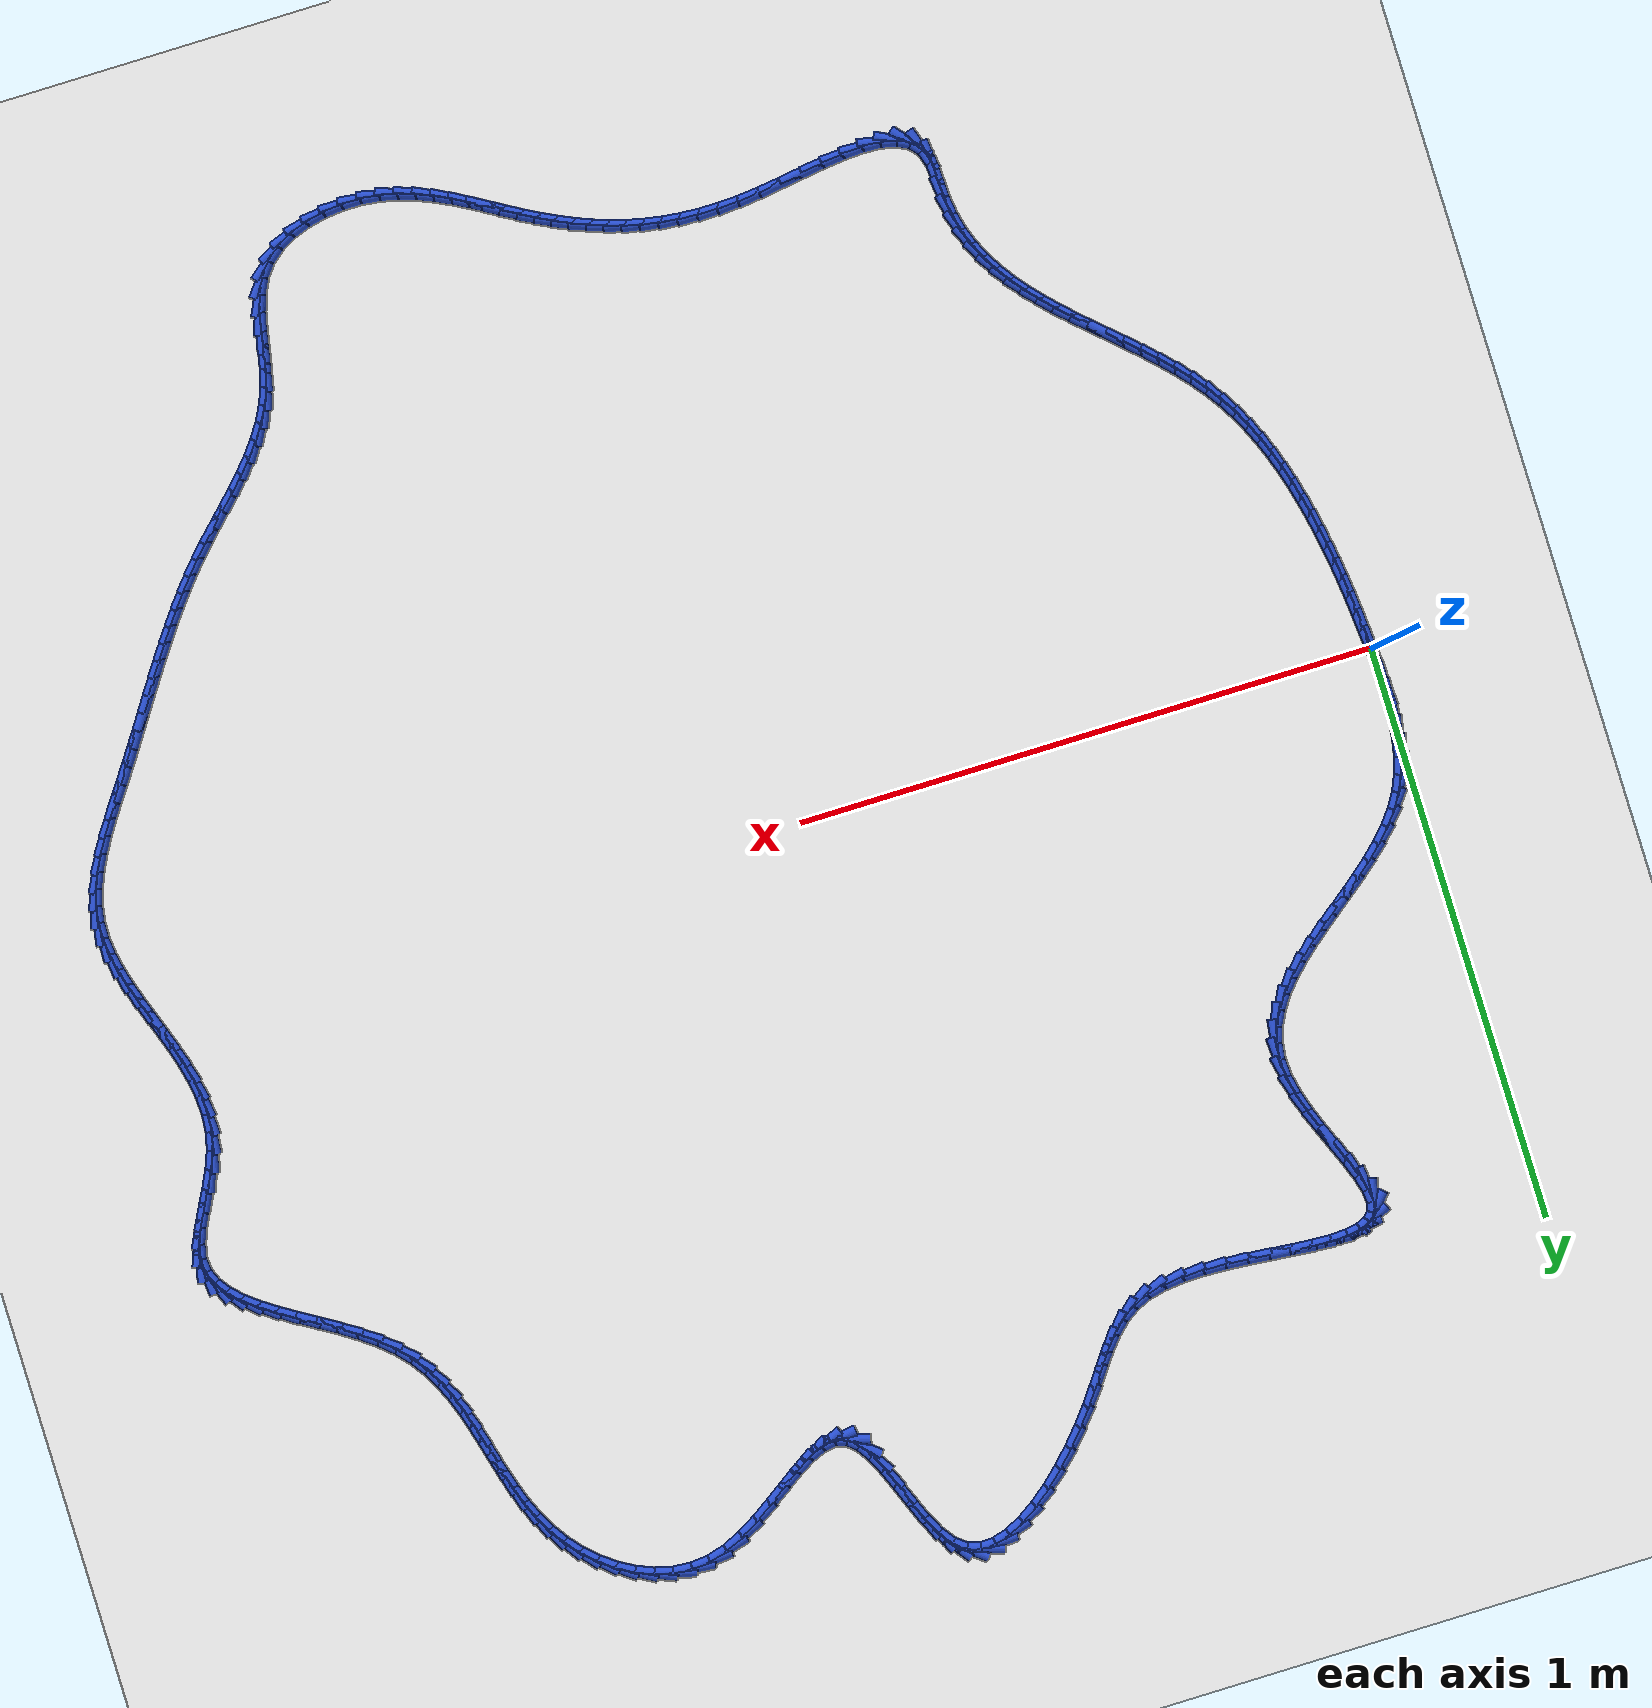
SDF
<sdf version="1.6">
 <world name="default">
  <light name="sun" type="directional">
   <pose>0 0 10 0 -0 0</pose>
   <diffuse>0.8 0.8 0.8 1</diffuse>
   <specular>0.2 0.2 0.2 1</specular>
   <attenuation>
    <range>1000</range>
    <constant>0.9</constant>
    <linear>0.01</linear>
    <quadratic>0.001</quadratic>
   </attenuation>
   <direction>-0.5 0.1 -0.9</direction>
  </light>
  <model name="ground_plane">
   <static>1</static>
   <link name="link">
    <collision name="collision">
     <geometry><plane><normal>0 0 1</normal><size>100 100</size></plane></geometry>
     <surface><friction><ode><mu>100</mu><mu2>50</mu2></ode></friction></surface>
    </collision>
    <visual name="visual">
     <cast_shadows>0</cast_shadows>
     <geometry><plane><normal>0 0 1</normal><size>100 100</size></plane></geometry>
     <material>
      <script><uri>file://media/materials/scripts/gazebo.material</uri><name>Gazebo/WhiteGlow</name></script>
     </material>
    </visual>
   </link>
  </model>
  <gravity>0 0 -9.8</gravity>
  <magnetic_field>6e-06 2.3e-05 -4.2e-05</magnetic_field>
  <atmosphere type="adiabatic"/>
  <physics name="default_physics" default="0" type="ode">
   <max_step_size>0.001</max_step_size>
   <real_time_factor>1</real_time_factor>
   <real_time_update_rate>1000</real_time_update_rate>
  </physics>
  <scene><ambient>0.4 0.4 0.4 1</ambient><background>0.7 0.7 0.7 1</background><shadows>1</shadows></scene>
  <spherical_coordinates>
   <surface_model>EARTH_WGS84</surface_model>
   <latitude_deg>0</latitude_deg>
   <longitude_deg>0</longitude_deg>
   <elevation>0</elevation>
   <heading_deg>0</heading_deg>
  </spherical_coordinates>
  <model name="line">
   <link name="link_0">
    <pose>-9.75781955236954e-18 -8.326672684688674e-17 0.01 0 1.57 -1.511199921775227</pose>
    <collision name="collision">
     <geometry><cylinder><radius>0.01</radius><length>0.08</length></cylinder></geometry>
    </collision>
    <visual name="visual">
     <material>
      <script><name>Gazebo/Blue</name><uri>file://media/materials/scripts/gazebo.material</uri></script>
     </material>
     <geometry><cylinder><radius>0.01</radius><length>0.08</length></cylinder></geometry>
    </visual>
   </link>
   <link name="link_1">
    <pose>-0.0018788935683571061 0.03148962758798921 0.01 0 1.57 -1.5325228419579033</pose>
    <collision name="collision">
     <geometry><cylinder><radius>0.01</radius><length>0.08</length></cylinder></geometry>
    </collision>
    <visual name="visual">
     <material>
      <script><name>Gazebo/Blue</name><uri>file://media/materials/scripts/gazebo.material</uri></script>
     </material>
     <geometry><cylinder><radius>0.01</radius><length>0.08</length></cylinder></geometry>
    </visual>
   </link>
   <link name="link_2">
    <pose>-0.003091062676038948 0.0631454114593483 0.01 0 1.57 -1.5673808474522573</pose>
    <collision name="collision">
     <geometry><cylinder><radius>0.01</radius><length>0.08</length></cylinder></geometry>
    </collision>
    <visual name="visual">
     <material>
      <script><name>Gazebo/Blue</name><uri>file://media/materials/scripts/gazebo.material</uri></script>
     </material>
     <geometry><cylinder><radius>0.01</radius><length>0.08</length></cylinder></geometry>
    </visual>
   </link>
   <link name="link_3">
    <pose>-0.0031988975344590114 0.09471768237245247 0.01 0 1.57 1.5249210132544264</pose>
    <collision name="collision">
     <geometry><cylinder><radius>0.01</radius><length>0.08</length></cylinder></geometry>
    </collision>
    <visual name="visual">
     <material>
      <script><name>Gazebo/Blue</name><uri>file://media/materials/scripts/gazebo.material</uri></script>
     </material>
     <geometry><cylinder><radius>0.01</radius><length>0.08</length></cylinder></geometry>
    </visual>
   </link>
   <link name="link_4">
    <pose>-0.0017647883550307745 0.12595677108567713 0.01 0 1.57 1.459900204618824</pose>
    <collision name="collision">
     <geometry><cylinder><radius>0.01</radius><length>0.08</length></cylinder></geometry>
    </collision>
    <visual name="visual">
     <material>
      <script><name>Gazebo/Blue</name><uri>file://media/materials/scripts/gazebo.material</uri></script>
     </material>
     <geometry><cylinder><radius>0.01</radius><length>0.08</length></cylinder></geometry>
    </visual>
   </link>
   <link name="link_5">
    <pose>0.001648874650832295 0.1566130083573974 0.01 0 1.57 1.3777220439233588</pose>
    <collision name="collision">
     <geometry><cylinder><radius>0.01</radius><length>0.08</length></cylinder></geometry>
    </collision>
    <visual name="visual">
     <material>
      <script><name>Gazebo/Blue</name><uri>file://media/materials/scripts/gazebo.material</uri></script>
     </material>
     <geometry><cylinder><radius>0.01</radius><length>0.08</length></cylinder></geometry>
    </visual>
   </link>
   <link name="link_6">
    <pose>0.007479701271716713 0.18643672494598856 0.01 0 1.57 1.2773252558742256</pose>
    <collision name="collision">
     <geometry><cylinder><radius>0.01</radius><length>0.08</length></cylinder></geometry>
    </collision>
    <visual name="visual">
     <material>
      <script><name>Gazebo/Blue</name><uri>file://media/materials/scripts/gazebo.material</uri></script>
     </material>
     <geometry><cylinder><radius>0.01</radius><length>0.08</length></cylinder></geometry>
    </visual>
   </link>
   <link name="link_7">
    <pose>0.016165301296209016 0.21517825160982598 0.01 0 1.57 1.1588069050394254</pose>
    <collision name="collision">
     <geometry><cylinder><radius>0.01</radius><length>0.08</length></cylinder></geometry>
    </collision>
    <visual name="visual">
     <material>
      <script><name>Gazebo/Blue</name><uri>file://media/materials/scripts/gazebo.material</uri></script>
     </material>
     <geometry><cylinder><radius>0.01</radius><length>0.08</length></cylinder></geometry>
    </visual>
   </link>
   <link name="link_8">
    <pose>0.02814328451289572 0.24258791910728503 0.01 0 1.57 1.0272415689124124</pose>
    <collision name="collision">
     <geometry><cylinder><radius>0.01</radius><length>0.08</length></cylinder></geometry>
    </collision>
    <visual name="visual">
     <material>
      <script><name>Gazebo/Blue</name><uri>file://media/materials/scripts/gazebo.material</uri></script>
     </material>
     <geometry><cylinder><radius>0.01</radius><length>0.08</length></cylinder></geometry>
    </visual>
   </link>
   <link name="link_9">
    <pose>0.04377279549229901 0.26845294506043443 0.01 0 1.57 0.9093564041124712</pose>
    <collision name="collision">
     <geometry><cylinder><radius>0.01</radius><length>0.08</length></cylinder></geometry>
    </collision>
    <visual name="visual">
     <material>
      <script><name>Gazebo/Blue</name><uri>file://media/materials/scripts/gazebo.material</uri></script>
     </material>
     <geometry><cylinder><radius>0.01</radius><length>0.08</length></cylinder></geometry>
    </visual>
   </link>
   <link name="link_10">
    <pose>0.06277278021340472 0.2928615074246651 0.01 0 1.57 0.8167476944167987</pose>
    <collision name="collision">
     <geometry><cylinder><radius>0.01</radius><length>0.08</length></cylinder></geometry>
    </collision>
    <visual name="visual">
     <material>
      <script><name>Gazebo/Blue</name><uri>file://media/materials/scripts/gazebo.material</uri></script>
     </material>
     <geometry><cylinder><radius>0.01</radius><length>0.08</length></cylinder></geometry>
    </visual>
   </link>
   <link name="link_11">
    <pose>0.08454982922023695 0.31604862389707283 0.01 0 1.57 0.7473552997154909</pose>
    <collision name="collision">
     <geometry><cylinder><radius>0.01</radius><length>0.08</length></cylinder></geometry>
    </collision>
    <visual name="visual">
     <material>
      <script><name>Gazebo/Blue</name><uri>file://media/materials/scripts/gazebo.material</uri></script>
     </material>
     <geometry><cylinder><radius>0.01</radius><length>0.08</length></cylinder></geometry>
    </visual>
   </link>
   <link name="link_12">
    <pose>0.1085084251450236 0.3382503031138856 0.01 0 1.57 0.6985396626724754</pose>
    <collision name="collision">
     <geometry><cylinder><radius>0.01</radius><length>0.08</length></cylinder></geometry>
    </collision>
    <visual name="visual">
     <material>
      <script><name>Gazebo/Blue</name><uri>file://media/materials/scripts/gazebo.material</uri></script>
     </material>
     <geometry><cylinder><radius>0.01</radius><length>0.08</length></cylinder></geometry>
    </visual>
   </link>
   <link name="link_13">
    <pose>0.1340530506199926 0.3597025537113314 0.01 0 1.57 0.668058092013355</pose>
    <collision name="collision">
     <geometry><cylinder><radius>0.01</radius><length>0.08</length></cylinder></geometry>
    </collision>
    <visual name="visual">
     <material>
      <script><name>Gazebo/Blue</name><uri>file://media/materials/scripts/gazebo.material</uri></script>
     </material>
     <geometry><cylinder><radius>0.01</radius><length>0.08</length></cylinder></geometry>
    </visual>
   </link>
   <link name="link_14">
    <pose>0.1605881882773719 0.3806413843256385 0.01 0 1.57 0.6544330675874</pose>
    <collision name="collision">
     <geometry><cylinder><radius>0.01</radius><length>0.08</length></cylinder></geometry>
    </collision>
    <visual name="visual">
     <material>
      <script><name>Gazebo/Blue</name><uri>file://media/materials/scripts/gazebo.material</uri></script>
     </material>
     <geometry><cylinder><radius>0.01</radius><length>0.08</length></cylinder></geometry>
    </visual>
   </link>
   <link name="link_15">
    <pose>0.18751832074938934 0.40130280359303455 0.01 0 1.57 0.6570756806640027</pose>
    <collision name="collision">
     <geometry><cylinder><radius>0.01</radius><length>0.08</length></cylinder></geometry>
    </collision>
    <visual name="visual">
     <material>
      <script><name>Gazebo/Blue</name><uri>file://media/materials/scripts/gazebo.material</uri></script>
     </material>
     <geometry><cylinder><radius>0.01</radius><length>0.08</length></cylinder></geometry>
    </visual>
   </link>
   <link name="link_16">
    <pose>0.2142479306682729 0.4219228201497477 0.01 0 1.57 0.6763322537236033</pose>
    <collision name="collision">
     <geometry><cylinder><radius>0.01</radius><length>0.08</length></cylinder></geometry>
    </collision>
    <visual name="visual">
     <material>
      <script><name>Gazebo/Blue</name><uri>file://media/materials/scripts/gazebo.material</uri></script>
     </material>
     <geometry><cylinder><radius>0.01</radius><length>0.08</length></cylinder></geometry>
    </visual>
   </link>
   <link name="link_17">
    <pose>0.24018150066625055 0.4427374426320062 0.01 0 1.57 0.7135201583428747</pose>
    <collision name="collision">
     <geometry><cylinder><radius>0.01</radius><length>0.08</length></cylinder></geometry>
    </collision>
    <visual name="visual">
     <material>
      <script><name>Gazebo/Blue</name><uri>file://media/materials/scripts/gazebo.material</uri></script>
     </material>
     <geometry><cylinder><radius>0.01</radius><length>0.08</length></cylinder></geometry>
    </visual>
   </link>
   <link name="link_18">
    <pose>0.2647235133755502 0.46398267967603796 0.01 0 1.57 0.7709371945820565</pose>
    <collision name="collision">
     <geometry><cylinder><radius>0.01</radius><length>0.08</length></cylinder></geometry>
    </collision>
    <visual name="visual">
     <material>
      <script><name>Gazebo/Blue</name><uri>file://media/materials/scripts/gazebo.material</uri></script>
     </material>
     <geometry><cylinder><radius>0.01</radius><length>0.08</length></cylinder></geometry>
    </visual>
   </link>
   <link name="link_19">
    <pose>0.2872784514283997 0.4858945399180709 0.01 0 1.57 0.8517264316414026</pose>
    <collision name="collision">
     <geometry><cylinder><radius>0.01</radius><length>0.08</length></cylinder></geometry>
    </collision>
    <visual name="visual">
     <material>
      <script><name>Gazebo/Blue</name><uri>file://media/materials/scripts/gazebo.material</uri></script>
     </material>
     <geometry><cylinder><radius>0.01</radius><length>0.08</length></cylinder></geometry>
    </visual>
   </link>
   <link name="link_20">
    <pose>0.3072507974570271 0.5087090319943331 0.01 0 1.57 0.9593130246366601</pose>
    <collision name="collision">
     <geometry><cylinder><radius>0.01</radius><length>0.08</length></cylinder></geometry>
    </collision>
    <visual name="visual">
     <material>
      <script><name>Gazebo/Blue</name><uri>file://media/materials/scripts/gazebo.material</uri></script>
     </material>
     <geometry><cylinder><radius>0.01</radius><length>0.08</length></cylinder></geometry>
    </visual>
   </link>
   <link name="link_21">
    <pose>0.32404503409366026 0.5326621645410528 0.01 0 1.57 1.0959450255256458</pose>
    <collision name="collision">
     <geometry><cylinder><radius>0.01</radius><length>0.08</length></cylinder></geometry>
    </collision>
    <visual name="visual">
     <material>
      <script><name>Gazebo/Blue</name><uri>file://media/materials/scripts/gazebo.material</uri></script>
     </material>
     <geometry><cylinder><radius>0.01</radius><length>0.08</length></cylinder></geometry>
    </visual>
   </link>
   <link name="link_22">
    <pose>0.33706564397052713 0.5579899461944575 0.01 0 1.57 1.2600442952651378</pose>
    <collision name="collision">
     <geometry><cylinder><radius>0.01</radius><length>0.08</length></cylinder></geometry>
    </collision>
    <visual name="visual">
     <material>
      <script><name>Gazebo/Blue</name><uri>file://media/materials/scripts/gazebo.material</uri></script>
     </material>
     <geometry><cylinder><radius>0.01</radius><length>0.08</length></cylinder></geometry>
    </visual>
   </link>
   <link name="link_23">
    <pose>0.3457171097198556 0.5849283855907759 0.01 0 1.57 1.443409605075324</pose>
    <collision name="collision">
     <geometry><cylinder><radius>0.01</radius><length>0.08</length></cylinder></geometry>
    </collision>
    <visual name="visual">
     <material>
      <script><name>Gazebo/Blue</name><uri>file://media/materials/scripts/gazebo.material</uri></script>
     </material>
     <geometry><cylinder><radius>0.01</radius><length>0.08</length></cylinder></geometry>
    </visual>
   </link>
   <link name="link_24">
    <pose>0.34940391397387377 0.6137134913662359 0.01 0 1.57 -1.511514143034651</pose>
    <collision name="collision">
     <geometry><cylinder><radius>0.01</radius><length>0.08</length></cylinder></geometry>
    </collision>
    <visual name="visual">
     <material>
      <script><name>Gazebo/Blue</name><uri>file://media/materials/scripts/gazebo.material</uri></script>
     </material>
     <geometry><cylinder><radius>0.01</radius><length>0.08</length></cylinder></geometry>
    </visual>
   </link>
   <link name="link_25">
    <pose>0.3475731662856283 0.6445592265192032 0.01 0 1.57 -1.3617061272588245</pose>
    <collision name="collision">
     <geometry><cylinder><radius>0.01</radius><length>0.08</length></cylinder></geometry>
    </collision>
    <visual name="visual">
     <material>
      <script><name>Gazebo/Blue</name><uri>file://media/materials/scripts/gazebo.material</uri></script>
     </material>
     <geometry><cylinder><radius>0.01</radius><length>0.08</length></cylinder></geometry>
    </visual>
   </link>
   <link name="link_26">
    <pose>0.34065296901439907 0.6771722077106695 0.01 0 1.57 -1.265019465220156</pose>
    <collision name="collision">
     <geometry><cylinder><radius>0.01</radius><length>0.08</length></cylinder></geometry>
    </collision>
    <visual name="visual">
     <material>
      <script><name>Gazebo/Blue</name><uri>file://media/materials/scripts/gazebo.material</uri></script>
     </material>
     <geometry><cylinder><radius>0.01</radius><length>0.08</length></cylinder></geometry>
    </visual>
   </link>
   <link name="link_27">
    <pose>0.3300527361134496 0.7107515403947458 0.01 0 1.57 -1.2072986790704372</pose>
    <collision name="collision">
     <geometry><cylinder><radius>0.01</radius><length>0.08</length></cylinder></geometry>
    </collision>
    <visual name="visual">
     <material>
      <script><name>Gazebo/Blue</name><uri>file://media/materials/scripts/gazebo.material</uri></script>
     </material>
     <geometry><cylinder><radius>0.01</radius><length>0.08</length></cylinder></geometry>
    </visual>
   </link>
   <link name="link_28">
    <pose>0.31722457221441464 0.7444742514137802 0.01 0 1.57 -1.180241004380367</pose>
    <collision name="collision">
     <geometry><cylinder><radius>0.01</radius><length>0.08</length></cylinder></geometry>
    </collision>
    <visual name="visual">
     <material>
      <script><name>Gazebo/Blue</name><uri>file://media/materials/scripts/gazebo.material</uri></script>
     </material>
     <geometry><cylinder><radius>0.01</radius><length>0.08</length></cylinder></geometry>
    </visual>
   </link>
   <link name="link_29">
    <pose>0.30362058194892955 0.7775173676101204 0.01 0 1.57 -1.1818053028943247</pose>
    <collision name="collision">
     <geometry><cylinder><radius>0.01</radius><length>0.08</length></cylinder></geometry>
    </collision>
    <visual name="visual">
     <material>
      <script><name>Gazebo/Blue</name><uri>file://media/materials/scripts/gazebo.material</uri></script>
     </material>
     <geometry><cylinder><radius>0.01</radius><length>0.08</length></cylinder></geometry>
    </visual>
   </link>
   <link name="link_30">
    <pose>0.2906928699486294 0.8090579158261135 0.01 0 1.57 -1.2167242451135813</pose>
    <collision name="collision">
     <geometry><cylinder><radius>0.01</radius><length>0.08</length></cylinder></geometry>
    </collision>
    <visual name="visual">
     <material>
      <script><name>Gazebo/Blue</name><uri>file://media/materials/scripts/gazebo.material</uri></script>
     </material>
     <geometry><cylinder><radius>0.01</radius><length>0.08</length></cylinder></geometry>
    </visual>
   </link>
   <link name="link_31">
    <pose>0.2798935408451488 0.8382729229041075 0.01 0 1.57 -1.30062787033472</pose>
    <collision name="collision">
     <geometry><cylinder><radius>0.01</radius><length>0.08</length></cylinder></geometry>
    </collision>
    <visual name="visual">
     <material>
      <script><name>Gazebo/Blue</name><uri>file://media/materials/scripts/gazebo.material</uri></script>
     </material>
     <geometry><cylinder><radius>0.01</radius><length>0.08</length></cylinder></geometry>
    </visual>
   </link>
   <link name="link_32">
    <pose>0.27267469927012306 0.86433941568645 0.01 0 1.57 -1.4721696880536552</pose>
    <collision name="collision">
     <geometry><cylinder><radius>0.01</radius><length>0.08</length></cylinder></geometry>
    </collision>
    <visual name="visual">
     <material>
      <script><name>Gazebo/Blue</name><uri>file://media/materials/scripts/gazebo.material</uri></script>
     </material>
     <geometry><cylinder><radius>0.01</radius><length>0.08</length></cylinder></geometry>
    </visual>
   </link>
   <link name="link_33">
    <pose>0.27048844985518705 0.8864344210154884 0.01 0 1.57 1.3277084426575376</pose>
    <collision name="collision">
     <geometry><cylinder><radius>0.01</radius><length>0.08</length></cylinder></geometry>
    </collision>
    <visual name="visual">
     <material>
      <script><name>Gazebo/Blue</name><uri>file://media/materials/scripts/gazebo.material</uri></script>
     </material>
     <geometry><cylinder><radius>0.01</radius><length>0.08</length></cylinder></geometry>
    </visual>
   </link>
   <link name="link_34">
    <pose>0.2747799939907737 0.903739593108168 0.01 0 1.57 0.8164979542598615</pose>
    <collision name="collision">
     <geometry><cylinder><radius>0.01</radius><length>0.08</length></cylinder></geometry>
    </collision>
    <visual name="visual">
     <material>
      <script><name>Gazebo/Blue</name><uri>file://media/materials/scripts/gazebo.material</uri></script>
     </material>
     <geometry><cylinder><radius>0.01</radius><length>0.08</length></cylinder></geometry>
    </visual>
   </link>
   <link name="link_35">
    <pose>0.28624393927247543 0.9159397235566972 0.01 0 1.57 0.40721604151239205</pose>
    <collision name="collision">
     <geometry><cylinder><radius>0.01</radius><length>0.08</length></cylinder></geometry>
    </collision>
    <visual name="visual">
     <material>
      <script><name>Gazebo/Blue</name><uri>file://media/materials/scripts/gazebo.material</uri></script>
     </material>
     <geometry><cylinder><radius>0.01</radius><length>0.08</length></cylinder></geometry>
    </visual>
   </link>
   <link name="link_36">
    <pose>0.3041605986678024 0.9236676326898843 0.01 0 1.57 0.16837543645940953</pose>
    <collision name="collision">
     <geometry><cylinder><radius>0.01</radius><length>0.08</length></cylinder></geometry>
    </collision>
    <visual name="visual">
     <material>
      <script><name>Gazebo/Blue</name><uri>file://media/materials/scripts/gazebo.material</uri></script>
     </material>
     <geometry><cylinder><radius>0.01</radius><length>0.08</length></cylinder></geometry>
    </visual>
   </link>
   <link name="link_37">
    <pose>0.3276536985306626 0.9276611038382451 0.01 0 1.57 0.03534182285236578</pose>
    <collision name="collision">
     <geometry><cylinder><radius>0.01</radius><length>0.08</length></cylinder></geometry>
    </collision>
    <visual name="visual">
     <material>
      <script><name>Gazebo/Blue</name><uri>file://media/materials/scripts/gazebo.material</uri></script>
     </material>
     <geometry><cylinder><radius>0.01</radius><length>0.08</length></cylinder></geometry>
    </visual>
   </link>
   <link name="link_38">
    <pose>0.3558469652149644 0.9286579203322948 0.01 0 1.57 -0.03939767893711735</pose>
    <collision name="collision">
     <geometry><cylinder><radius>0.01</radius><length>0.08</length></cylinder></geometry>
    </collision>
    <visual name="visual">
     <material>
      <script><name>Gazebo/Blue</name><uri>file://media/materials/scripts/gazebo.material</uri></script>
     </material>
     <geometry><cylinder><radius>0.01</radius><length>0.08</length></cylinder></geometry>
    </visual>
   </link>
   <link name="link_39">
    <pose>0.387864125074616 0.9273958655025492 0.01 0 1.57 -0.07943099303169561</pose>
    <collision name="collision">
     <geometry><cylinder><radius>0.01</radius><length>0.08</length></cylinder></geometry>
    </collision>
    <visual name="visual">
     <material>
      <script><name>Gazebo/Blue</name><uri>file://media/materials/scripts/gazebo.material</uri></script>
     </material>
     <geometry><cylinder><radius>0.01</radius><length>0.08</length></cylinder></geometry>
    </visual>
   </link>
   <link name="link_40">
    <pose>0.4228289044635256 0.9246127226795235 0.01 0 1.57 -0.09600044534519736</pose>
    <collision name="collision">
     <geometry><cylinder><radius>0.01</radius><length>0.08</length></cylinder></geometry>
    </collision>
    <visual name="visual">
     <material>
      <script><name>Gazebo/Blue</name><uri>file://media/materials/scripts/gazebo.material</uri></script>
     </material>
     <geometry><cylinder><radius>0.01</radius><length>0.08</length></cylinder></geometry>
    </visual>
   </link>
   <link name="link_41">
    <pose>0.45986502973560106 0.9210462751937329 0.01 0 1.57 -0.09419739761582085</pose>
    <collision name="collision">
     <geometry><cylinder><radius>0.01</radius><length>0.08</length></cylinder></geometry>
    </collision>
    <visual name="visual">
     <material>
      <script><name>Gazebo/Blue</name><uri>file://media/materials/scripts/gazebo.material</uri></script>
     </material>
     <geometry><cylinder><radius>0.01</radius><length>0.08</length></cylinder></geometry>
    </visual>
   </link>
   <link name="link_42">
    <pose>0.4980962272447507 0.9174343063756931 0.01 0 1.57 -0.07559386525455299</pose>
    <collision name="collision">
     <geometry><cylinder><radius>0.01</radius><length>0.08</length></cylinder></geometry>
    </collision>
    <visual name="visual">
     <material>
      <script><name>Gazebo/Blue</name><uri>file://media/materials/scripts/gazebo.material</uri></script>
     </material>
     <geometry><cylinder><radius>0.01</radius><length>0.08</length></cylinder></geometry>
    </visual>
   </link>
   <link name="link_43">
    <pose>0.536646223344883 0.91451459955592 0.01 0 1.57 -0.039189260556959156</pose>
    <collision name="collision">
     <geometry><cylinder><radius>0.01</radius><length>0.08</length></cylinder></geometry>
    </collision>
    <visual name="visual">
     <material>
      <script><name>Gazebo/Blue</name><uri>file://media/materials/scripts/gazebo.material</uri></script>
     </material>
     <geometry><cylinder><radius>0.01</radius><length>0.08</length></cylinder></geometry>
    </visual>
   </link>
   <link name="link_44">
    <pose>0.5746387443899055 0.9130249380649282 0.01 0 1.57 0.0185479258220122</pose>
    <collision name="collision">
     <geometry><cylinder><radius>0.01</radius><length>0.08</length></cylinder></geometry>
    </collision>
    <visual name="visual">
     <material>
      <script><name>Gazebo/Blue</name><uri>file://media/materials/scripts/gazebo.material</uri></script>
     </material>
     <geometry><cylinder><radius>0.01</radius><length>0.08</length></cylinder></geometry>
    </visual>
   </link>
   <link name="link_45">
    <pose>0.6111975167337269 0.9137031052332338 0.01 0 1.57 0.10426028003501539</pose>
    <collision name="collision">
     <geometry><cylinder><radius>0.01</radius><length>0.08</length></cylinder></geometry>
    </collision>
    <visual name="visual">
     <material>
      <script><name>Gazebo/Blue</name><uri>file://media/materials/scripts/gazebo.material</uri></script>
     </material>
     <geometry><cylinder><radius>0.01</radius><length>0.08</length></cylinder></geometry>
    </visual>
   </link>
   <link name="link_46">
    <pose>0.6454462667302554 0.917286884391352 0.01 0 1.57 0.22859888851819138</pose>
    <collision name="collision">
     <geometry><cylinder><radius>0.01</radius><length>0.08</length></cylinder></geometry>
    </collision>
    <visual name="visual">
     <material>
      <script><name>Gazebo/Blue</name><uri>file://media/materials/scripts/gazebo.material</uri></script>
     </material>
     <geometry><cylinder><radius>0.01</radius><length>0.08</length></cylinder></geometry>
    </visual>
   </link>
   <link name="link_47">
    <pose>0.6765087207333988 0.9245140588697981 0.01 0 1.57 0.402550118424764</pose>
    <collision name="collision">
     <geometry><cylinder><radius>0.01</radius><length>0.08</length></cylinder></geometry>
    </collision>
    <visual name="visual">
     <material>
      <script><name>Gazebo/Blue</name><uri>file://media/materials/scripts/gazebo.material</uri></script>
     </material>
     <geometry><cylinder><radius>0.01</radius><length>0.08</length></cylinder></geometry>
    </visual>
   </link>
   <link name="link_48">
    <pose>0.7036090198832176 0.9360534321632212 0.01 0 1.57 0.5911672361322423</pose>
    <collision name="collision">
     <geometry><cylinder><radius>0.01</radius><length>0.08</length></cylinder></geometry>
    </collision>
    <visual name="visual">
     <material>
      <script><name>Gazebo/Blue</name><uri>file://media/materials/scripts/gazebo.material</uri></script>
     </material>
     <geometry><cylinder><radius>0.01</radius><length>0.08</length></cylinder></geometry>
    </visual>
   </link>
   <link name="link_49">
    <pose>0.7270828880962285 0.951810207101362 0.01 0 1.57 0.7489096195645445</pose>
    <collision name="collision">
     <geometry><cylinder><radius>0.01</radius><length>0.08</length></cylinder></geometry>
    </collision>
    <visual name="visual">
     <material>
      <script><name>Gazebo/Blue</name><uri>file://media/materials/scripts/gazebo.material</uri></script>
     </material>
     <geometry><cylinder><radius>0.01</radius><length>0.08</length></cylinder></geometry>
    </visual>
   </link>
   <link name="link_50">
    <pose>0.7479575900101076 0.9712145333144399 0.01 0 1.57 0.8609130629755704</pose>
    <collision name="collision">
     <geometry><cylinder><radius>0.01</radius><length>0.08</length></cylinder></geometry>
    </collision>
    <visual name="visual">
     <material>
      <script><name>Gazebo/Blue</name><uri>file://media/materials/scripts/gazebo.material</uri></script>
     </material>
     <geometry><cylinder><radius>0.01</radius><length>0.08</length></cylinder></geometry>
    </visual>
   </link>
   <link name="link_51">
    <pose>0.7672708181295743 0.9936893970199473 0.01 0 1.57 0.9256783350234769</pose>
    <collision name="collision">
     <geometry><cylinder><radius>0.01</radius><length>0.08</length></cylinder></geometry>
    </collision>
    <visual name="visual">
     <material>
      <script><name>Gazebo/Blue</name><uri>file://media/materials/scripts/gazebo.material</uri></script>
     </material>
     <geometry><cylinder><radius>0.01</radius><length>0.08</length></cylinder></geometry>
    </visual>
   </link>
   <link name="link_52">
    <pose>0.7860602649593482 1.018657784435378 0.01 0 1.57 0.948091656365511</pose>
    <collision name="collision">
     <geometry><cylinder><radius>0.01</radius><length>0.08</length></cylinder></geometry>
    </collision>
    <visual name="visual">
     <material>
      <script><name>Gazebo/Blue</name><uri>file://media/materials/scripts/gazebo.material</uri></script>
     </material>
     <geometry><cylinder><radius>0.01</radius><length>0.08</length></cylinder></geometry>
    </visual>
   </link>
   <link name="link_53">
    <pose>0.8053636230041479 1.0455426817782247 0.01 0 1.57 0.9344381253500879</pose>
    <collision name="collision">
     <geometry><cylinder><radius>0.01</radius><length>0.08</length></cylinder></geometry>
    </collision>
    <visual name="visual">
     <material>
      <script><name>Gazebo/Blue</name><uri>file://media/materials/scripts/gazebo.material</uri></script>
     </material>
     <geometry><cylinder><radius>0.01</radius><length>0.08</length></cylinder></geometry>
    </visual>
   </link>
   <link name="link_54">
    <pose>0.8262185847686929 1.0737670752659803 0.01 0 1.57 0.8937115167652907</pose>
    <collision name="collision">
     <geometry><cylinder><radius>0.01</radius><length>0.08</length></cylinder></geometry>
    </collision>
    <visual name="visual">
     <material>
      <script><name>Gazebo/Blue</name><uri>file://media/materials/scripts/gazebo.material</uri></script>
     </material>
     <geometry><cylinder><radius>0.01</radius><length>0.08</length></cylinder></geometry>
    </visual>
   </link>
   <link name="link_55">
    <pose>0.8494861331020662 1.1027121700253792 0.01 0 1.57 0.8461845269887914</pose>
    <collision name="collision">
     <geometry><cylinder><radius>0.01</radius><length>0.08</length></cylinder></geometry>
    </collision>
    <visual name="visual">
     <material>
      <script><name>Gazebo/Blue</name><uri>file://media/materials/scripts/gazebo.material</uri></script>
     </material>
     <geometry><cylinder><radius>0.01</radius><length>0.08</length></cylinder></geometry>
    </visual>
   </link>
   <link name="link_56">
    <pose>0.8749813859970406 1.131511887726429 0.01 0 1.57 0.7952953578103186</pose>
    <collision name="collision">
     <geometry><cylinder><radius>0.01</radius><length>0.08</length></cylinder></geometry>
    </collision>
    <visual name="visual">
     <material>
      <script><name>Gazebo/Blue</name><uri>file://media/materials/scripts/gazebo.material</uri></script>
     </material>
     <geometry><cylinder><radius>0.01</radius><length>0.08</length></cylinder></geometry>
    </visual>
   </link>
   <link name="link_57">
    <pose>0.9021361060414731 1.1592095097913928 0.01 0 1.57 0.73705975357311</pose>
    <collision name="collision">
     <geometry><cylinder><radius>0.01</radius><length>0.08</length></cylinder></geometry>
    </collision>
    <visual name="visual">
     <material>
      <script><name>Gazebo/Blue</name><uri>file://media/materials/scripts/gazebo.material</uri></script>
     </material>
     <geometry><cylinder><radius>0.01</radius><length>0.08</length></cylinder></geometry>
    </visual>
   </link>
   <link name="link_58">
    <pose>0.9303814763297773 1.1848481806275644 0.01 0 1.57 0.6664002680586689</pose>
    <collision name="collision">
     <geometry><cylinder><radius>0.01</radius><length>0.08</length></cylinder></geometry>
    </collision>
    <visual name="visual">
     <material>
      <script><name>Gazebo/Blue</name><uri>file://media/materials/scripts/gazebo.material</uri></script>
     </material>
     <geometry><cylinder><radius>0.01</radius><length>0.08</length></cylinder></geometry>
    </visual>
   </link>
   <link name="link_59">
    <pose>0.9591486799563673 1.2074710446422376 0.01 0 1.57 0.5759359408535398</pose>
    <collision name="collision">
     <geometry><cylinder><radius>0.01</radius><length>0.08</length></cylinder></geometry>
    </collision>
    <visual name="visual">
     <material>
      <script><name>Gazebo/Blue</name><uri>file://media/materials/scripts/gazebo.material</uri></script>
     </material>
     <geometry><cylinder><radius>0.01</radius><length>0.08</length></cylinder></geometry>
    </visual>
   </link>
   <link name="link_60">
    <pose>0.987868900015656 1.2261212462427056 0.01 0 1.57 0.45416616963184747</pose>
    <collision name="collision">
     <geometry><cylinder><radius>0.01</radius><length>0.08</length></cylinder></geometry>
    </collision>
    <visual name="visual">
     <material>
      <script><name>Gazebo/Blue</name><uri>file://media/materials/scripts/gazebo.material</uri></script>
     </material>
     <geometry><cylinder><radius>0.01</radius><length>0.08</length></cylinder></geometry>
    </visual>
   </link>
   <link name="link_61">
    <pose>1.0159733196020575 1.239841929836262 0.01 0 1.57 0.2832017758984645</pose>
    <collision name="collision">
     <geometry><cylinder><radius>0.01</radius><length>0.08</length></cylinder></geometry>
    </collision>
    <visual name="visual">
     <material>
      <script><name>Gazebo/Blue</name><uri>file://media/materials/scripts/gazebo.material</uri></script>
     </material>
     <geometry><cylinder><radius>0.01</radius><length>0.08</length></cylinder></geometry>
    </visual>
   </link>
   <link name="link_62">
    <pose>1.0428931218099857 1.2476762398302008 0.01 0 1.57 0.03936082207266667</pose>
    <collision name="collision">
     <geometry><cylinder><radius>0.01</radius><length>0.08</length></cylinder></geometry>
    </collision>
    <visual name="visual">
     <material>
      <script><name>Gazebo/Blue</name><uri>file://media/materials/scripts/gazebo.material</uri></script>
     </material>
     <geometry><cylinder><radius>0.01</radius><length>0.08</length></cylinder></geometry>
    </visual>
   </link>
   <link name="link_63">
    <pose>1.0680594897338538 1.2486673206318148 0.01 0 1.57 -0.28967950859084945</pose>
    <collision name="collision">
     <geometry><cylinder><radius>0.01</radius><length>0.08</length></cylinder></geometry>
    </collision>
    <visual name="visual">
     <material>
      <script><name>Gazebo/Blue</name><uri>file://media/materials/scripts/gazebo.material</uri></script>
     </material>
     <geometry><cylinder><radius>0.01</radius><length>0.08</length></cylinder></geometry>
    </visual>
   </link>
   <link name="link_64">
    <pose>1.0909036064680755 1.2418583166483983 0.01 0 1.57 -0.6586504195495102</pose>
    <collision name="collision">
     <geometry><cylinder><radius>0.01</radius><length>0.08</length></cylinder></geometry>
    </collision>
    <visual name="visual">
     <material>
      <script><name>Gazebo/Blue</name><uri>file://media/materials/scripts/gazebo.material</uri></script>
     </material>
     <geometry><cylinder><radius>0.01</radius><length>0.08</length></cylinder></geometry>
    </visual>
   </link>
   <link name="link_65">
    <pose>1.1108935729754001 1.2263871882364186 0.01 0 1.57 -0.9339067698570097</pose>
    <collision name="collision">
     <geometry><cylinder><radius>0.01</radius><length>0.08</length></cylinder></geometry>
    </collision>
    <visual name="visual">
     <material>
      <script><name>Gazebo/Blue</name><uri>file://media/materials/scripts/gazebo.material</uri></script>
     </material>
     <geometry><cylinder><radius>0.01</radius><length>0.08</length></cylinder></geometry>
    </visual>
   </link>
   <link name="link_66">
    <pose>1.1281477401653455 1.2030619289553244 0.01 0 1.57 -1.0874279280124797</pose>
    <collision name="collision">
     <geometry><cylinder><radius>0.01</radius><length>0.08</length></cylinder></geometry>
    </collision>
    <visual name="visual">
     <material>
      <script><name>Gazebo/Blue</name><uri>file://media/materials/scripts/gazebo.material</uri></script>
     </material>
     <geometry><cylinder><radius>0.01</radius><length>0.08</length></cylinder></geometry>
    </visual>
   </link>
   <link name="link_67">
    <pose>1.1433403215445055 1.174118151079531 0.01 0 1.57 -1.1662053593688466</pose>
    <collision name="collision">
     <geometry><cylinder><radius>0.01</radius><length>0.08</length></cylinder></geometry>
    </collision>
    <visual name="visual">
     <material>
      <script><name>Gazebo/Blue</name><uri>file://media/materials/scripts/gazebo.material</uri></script>
     </material>
     <geometry><cylinder><radius>0.01</radius><length>0.08</length></cylinder></geometry>
    </visual>
   </link>
   <link name="link_68">
    <pose>1.1571634253390457 1.1418374257889317 0.01 0 1.57 -1.1951793816552505</pose>
    <collision name="collision">
     <geometry><cylinder><radius>0.01</radius><length>0.08</length></cylinder></geometry>
    </collision>
    <visual name="visual">
     <material>
      <script><name>Gazebo/Blue</name><uri>file://media/materials/scripts/gazebo.material</uri></script>
     </material>
     <geometry><cylinder><radius>0.01</radius><length>0.08</length></cylinder></geometry>
    </visual>
   </link>
   <link name="link_69">
    <pose>1.1703091597751303 1.1085013242634187 0.01 0 1.57 -1.181821434320776</pose>
    <collision name="collision">
     <geometry><cylinder><radius>0.01</radius><length>0.08</length></cylinder></geometry>
    </collision>
    <visual name="visual">
     <material>
      <script><name>Gazebo/Blue</name><uri>file://media/materials/scripts/gazebo.material</uri></script>
     </material>
     <geometry><cylinder><radius>0.01</radius><length>0.08</length></cylinder></geometry>
    </visual>
   </link>
   <link name="link_70">
    <pose>1.1834696330789247 1.0763914176828862 0.01 0 1.57 -1.1193541073777358</pose>
    <collision name="collision">
     <geometry><cylinder><radius>0.01</radius><length>0.08</length></cylinder></geometry>
    </collision>
    <visual name="visual">
     <material>
      <script><name>Gazebo/Blue</name><uri>file://media/materials/scripts/gazebo.material</uri></script>
     </material>
     <geometry><cylinder><radius>0.01</radius><length>0.08</length></cylinder></geometry>
    </visual>
   </link>
   <link name="link_71">
    <pose>1.1973369534765932 1.0477892772272264 0.01 0 1.57 -0.9810435060835496</pose>
    <collision name="collision">
     <geometry><cylinder><radius>0.01</radius><length>0.08</length></cylinder></geometry>
    </collision>
    <visual name="visual">
     <material>
      <script><name>Gazebo/Blue</name><uri>file://media/materials/scripts/gazebo.material</uri></script>
     </material>
     <geometry><cylinder><radius>0.01</radius><length>0.08</length></cylinder></geometry>
    </visual>
   </link>
   <link name="link_72">
    <pose>1.212603229194301 1.0249764740763325 0.01 0 1.57 -0.7040978147836128</pose>
    <collision name="collision">
     <geometry><cylinder><radius>0.01</radius><length>0.08</length></cylinder></geometry>
    </collision>
    <visual name="visual">
     <material>
      <script><name>Gazebo/Blue</name><uri>file://media/materials/scripts/gazebo.material</uri></script>
     </material>
     <geometry><cylinder><radius>0.01</radius><length>0.08</length></cylinder></geometry>
    </visual>
   </link>
   <link name="link_73">
    <pose>1.229960568333488 1.0102345788926677 0.01 0 1.57 -0.24901573664078291</pose>
    <collision name="collision">
     <geometry><cylinder><radius>0.01</radius><length>0.08</length></cylinder></geometry>
    </collision>
    <visual name="visual">
     <material>
      <script><name>Gazebo/Blue</name><uri>file://media/materials/scripts/gazebo.material</uri></script>
     </material>
     <geometry><cylinder><radius>0.01</radius><length>0.08</length></cylinder></geometry>
    </visual>
   </link>
   <link name="link_74">
    <pose>1.2499347809216996 1.0051552615206778 0.01 0 1.57 0.15409708749278433</pose>
    <collision name="collision">
     <geometry><cylinder><radius>0.01</radius><length>0.08</length></cylinder></geometry>
    </collision>
    <visual name="visual">
     <material>
      <script><name>Gazebo/Blue</name><uri>file://media/materials/scripts/gazebo.material</uri></script>
     </material>
     <geometry><cylinder><radius>0.01</radius><length>0.08</length></cylinder></geometry>
    </visual>
   </link>
   <link name="link_75">
    <pose>1.2724045308121492 1.0086454543055114 0.01 0 1.57 0.3957433033059598</pose>
    <collision name="collision">
     <geometry><cylinder><radius>0.01</radius><length>0.08</length></cylinder></geometry>
    </collision>
    <visual name="visual">
     <material>
      <script><name>Gazebo/Blue</name><uri>file://media/materials/scripts/gazebo.material</uri></script>
     </material>
     <geometry><cylinder><radius>0.01</radius><length>0.08</length></cylinder></geometry>
    </visual>
   </link>
   <link name="link_76">
    <pose>1.2970910851040345 1.018959116609497 0.01 0 1.57 0.524143859981627</pose>
    <collision name="collision">
     <geometry><cylinder><radius>0.01</radius><length>0.08</length></cylinder></geometry>
    </collision>
    <visual name="visual">
     <material>
      <script><name>Gazebo/Blue</name><uri>file://media/materials/scripts/gazebo.material</uri></script>
     </material>
     <geometry><cylinder><radius>0.01</radius><length>0.08</length></cylinder></geometry>
    </visual>
   </link>
   <link name="link_77">
    <pose>1.3237157108965545 1.0343502077949627 0.01 0 1.57 0.5847278744060506</pose>
    <collision name="collision">
     <geometry><cylinder><radius>0.01</radius><length>0.08</length></cylinder></geometry>
    </collision>
    <visual name="visual">
     <material>
      <script><name>Gazebo/Blue</name><uri>file://media/materials/scripts/gazebo.material</uri></script>
     </material>
     <geometry><cylinder><radius>0.01</radius><length>0.08</length></cylinder></geometry>
    </visual>
   </link>
   <link name="link_78">
    <pose>1.3519996752889067 1.0530726872242382 0.01 0 1.57 0.6003031076162122</pose>
    <collision name="collision">
     <geometry><cylinder><radius>0.01</radius><length>0.08</length></cylinder></geometry>
    </collision>
    <visual name="visual">
     <material>
      <script><name>Gazebo/Blue</name><uri>file://media/materials/scripts/gazebo.material</uri></script>
     </material>
     <geometry><cylinder><radius>0.01</radius><length>0.08</length></cylinder></geometry>
    </visual>
   </link>
   <link name="link_79">
    <pose>1.3816642453802892 1.073380514259651 0.01 0 1.57 0.5797709909957547</pose>
    <collision name="collision">
     <geometry><cylinder><radius>0.01</radius><length>0.08</length></cylinder></geometry>
    </collision>
    <visual name="visual">
     <material>
      <script><name>Gazebo/Blue</name><uri>file://media/materials/scripts/gazebo.material</uri></script>
     </material>
     <geometry><cylinder><radius>0.01</radius><length>0.08</length></cylinder></geometry>
    </visual>
   </link>
   <link name="link_80">
    <pose>1.4124306882699007 1.0935276482635312 0.01 0 1.57 0.523649729401626</pose>
    <collision name="collision">
     <geometry><cylinder><radius>0.01</radius><length>0.08</length></cylinder></geometry>
    </collision>
    <visual name="visual">
     <material>
      <script><name>Gazebo/Blue</name><uri>file://media/materials/scripts/gazebo.material</uri></script>
     </material>
     <geometry><cylinder><radius>0.01</radius><length>0.08</length></cylinder></geometry>
    </visual>
   </link>
   <link name="link_81">
    <pose>1.4440202710569392 1.1117680485982067 0.01 0 1.57 0.4261442454980627</pose>
    <collision name="collision">
     <geometry><cylinder><radius>0.01</radius><length>0.08</length></cylinder></geometry>
    </collision>
    <visual name="visual">
     <material>
      <script><name>Gazebo/Blue</name><uri>file://media/materials/scripts/gazebo.material</uri></script>
     </material>
     <geometry><cylinder><radius>0.01</radius><length>0.08</length></cylinder></geometry>
    </visual>
   </link>
   <link name="link_82">
    <pose>1.4761542608406026 1.1263556746260064 0.01 0 1.57 0.27692197553769354</pose>
    <collision name="collision">
     <geometry><cylinder><radius>0.01</radius><length>0.08</length></cylinder></geometry>
    </collision>
    <visual name="visual">
     <material>
      <script><name>Gazebo/Blue</name><uri>file://media/materials/scripts/gazebo.material</uri></script>
     </material>
     <geometry><cylinder><radius>0.01</radius><length>0.08</length></cylinder></geometry>
    </visual>
   </link>
   <link name="link_83">
    <pose>1.5085529504760595 1.135564183235079 0.01 0 1.57 0.09326714842904245</pose>
    <collision name="collision">
     <geometry><cylinder><radius>0.01</radius><length>0.08</length></cylinder></geometry>
    </collision>
    <visual name="visual">
     <material>
      <script><name>Gazebo/Blue</name><uri>file://media/materials/scripts/gazebo.material</uri></script>
     </material>
     <geometry><cylinder><radius>0.01</radius><length>0.08</length></cylinder></geometry>
    </visual>
   </link>
   <link name="link_84">
    <pose>1.5408910399275777 1.1385890405513708 0.01 0 1.57 -0.08343687490138052</pose>
    <collision name="collision">
     <geometry><cylinder><radius>0.01</radius><length>0.08</length></cylinder></geometry>
    </collision>
    <visual name="visual">
     <material>
      <script><name>Gazebo/Blue</name><uri>file://media/materials/scripts/gazebo.material</uri></script>
     </material>
     <geometry><cylinder><radius>0.01</radius><length>0.08</length></cylinder></geometry>
    </visual>
   </link>
   <link name="link_85">
    <pose>1.572779104178677 1.135922208677593 0.01 0 1.57 -0.2452281939316344</pose>
    <collision name="collision">
     <geometry><cylinder><radius>0.01</radius><length>0.08</length></cylinder></geometry>
    </collision>
    <visual name="visual">
     <material>
      <script><name>Gazebo/Blue</name><uri>file://media/materials/scripts/gazebo.material</uri></script>
     </material>
     <geometry><cylinder><radius>0.01</radius><length>0.08</length></cylinder></geometry>
    </visual>
   </link>
   <link name="link_86">
    <pose>1.6038229018506722 1.1281530282131438 0.01 0 1.57 -0.390877307131386</pose>
    <collision name="collision">
     <geometry><cylinder><radius>0.01</radius><length>0.08</length></cylinder></geometry>
    </collision>
    <visual name="visual">
     <material>
      <script><name>Gazebo/Blue</name><uri>file://media/materials/scripts/gazebo.material</uri></script>
     </material>
     <geometry><cylinder><radius>0.01</radius><length>0.08</length></cylinder></geometry>
    </visual>
   </link>
   <link name="link_87">
    <pose>1.633628191564875 1.115870839757421 0.01 0 1.57 -0.5220115262664327</pose>
    <collision name="collision">
     <geometry><cylinder><radius>0.01</radius><length>0.08</length></cylinder></geometry>
    </collision>
    <visual name="visual">
     <material>
      <script><name>Gazebo/Blue</name><uri>file://media/materials/scripts/gazebo.material</uri></script>
     </material>
     <geometry><cylinder><radius>0.01</radius><length>0.08</length></cylinder></geometry>
    </visual>
   </link>
   <link name="link_88">
    <pose>1.661800731942599 1.0996649839098245 0.01 0 1.57 -0.6418104622183876</pose>
    <collision name="collision">
     <geometry><cylinder><radius>0.01</radius><length>0.08</length></cylinder></geometry>
    </collision>
    <visual name="visual">
     <material>
      <script><name>Gazebo/Blue</name><uri>file://media/materials/scripts/gazebo.material</uri></script>
     </material>
     <geometry><cylinder><radius>0.01</radius><length>0.08</length></cylinder></geometry>
    </visual>
   </link>
   <link name="link_89">
    <pose>1.6879462816051585 1.0801248012697517 0.01 0 1.57 -0.7541289672191414</pose>
    <collision name="collision">
     <geometry><cylinder><radius>0.01</radius><length>0.08</length></cylinder></geometry>
    </collision>
    <visual name="visual">
     <material>
      <script><name>Gazebo/Blue</name><uri>file://media/materials/scripts/gazebo.material</uri></script>
     </material>
     <geometry><cylinder><radius>0.01</radius><length>0.08</length></cylinder></geometry>
    </visual>
   </link>
   <link name="link_90">
    <pose>1.7116705991738663 1.0578396324366015 0.01 0 1.57 -0.8631243238378926</pose>
    <collision name="collision">
     <geometry><cylinder><radius>0.01</radius><length>0.08</length></cylinder></geometry>
    </collision>
    <visual name="visual">
     <material>
      <script><name>Gazebo/Blue</name><uri>file://media/materials/scripts/gazebo.material</uri></script>
     </material>
     <geometry><cylinder><radius>0.01</radius><length>0.08</length></cylinder></geometry>
    </visual>
   </link>
   <link name="link_91">
    <pose>1.7325794432700363 1.0333988180097728 0.01 0 1.57 -0.9725801678028918</pose>
    <collision name="collision">
     <geometry><cylinder><radius>0.01</radius><length>0.08</length></cylinder></geometry>
    </collision>
    <visual name="visual">
     <material>
      <script><name>Gazebo/Blue</name><uri>file://media/materials/scripts/gazebo.material</uri></script>
     </material>
     <geometry><cylinder><radius>0.01</radius><length>0.08</length></cylinder></geometry>
    </visual>
   </link>
   <link name="link_92">
    <pose>1.7503127276946968 1.0073786687721302 0.01 0 1.57 -1.0753764190749566</pose>
    <collision name="collision">
     <geometry><cylinder><radius>0.01</radius><length>0.08</length></cylinder></geometry>
    </collision>
    <visual name="visual">
     <material>
      <script><name>Gazebo/Blue</name><uri>file://media/materials/scripts/gazebo.material</uri></script>
     </material>
     <geometry><cylinder><radius>0.01</radius><length>0.08</length></cylinder></geometry>
    </visual>
   </link>
   <link name="link_93">
    <pose>1.765020385625667 0.9801609288562344 0.01 0 1.57 -1.161549714665359</pose>
    <collision name="collision">
     <geometry><cylinder><radius>0.01</radius><length>0.08</length></cylinder></geometry>
    </collision>
    <visual name="visual">
     <material>
      <script><name>Gazebo/Blue</name><uri>file://media/materials/scripts/gazebo.material</uri></script>
     </material>
     <geometry><cylinder><radius>0.01</radius><length>0.08</length></cylinder></geometry>
    </visual>
   </link>
   <link name="link_94">
    <pose>1.7772444312501554 0.9519777679037197 0.01 0 1.57 -1.2288816464680574</pose>
    <collision name="collision">
     <geometry><cylinder><radius>0.01</radius><length>0.08</length></cylinder></geometry>
    </collision>
    <visual name="visual">
     <material>
      <script><name>Gazebo/Blue</name><uri>file://media/materials/scripts/gazebo.material</uri></script>
     </material>
     <geometry><cylinder><radius>0.01</radius><length>0.08</length></cylinder></geometry>
    </visual>
   </link>
   <link name="link_95">
    <pose>1.7875369337066558 0.9230575197055066 0.01 0 1.57 -1.2767127381516896</pose>
    <collision name="collision">
     <geometry><cylinder><radius>0.01</radius><length>0.08</length></cylinder></geometry>
    </collision>
    <visual name="visual">
     <material>
      <script><name>Gazebo/Blue</name><uri>file://media/materials/scripts/gazebo.material</uri></script>
     </material>
     <geometry><cylinder><radius>0.01</radius><length>0.08</length></cylinder></geometry>
    </visual>
   </link>
   <link name="link_96">
    <pose>1.7964499621336631 0.8936285180525148 0.01 0 1.57 -1.3050752545958397</pose>
    <collision name="collision">
     <geometry><cylinder><radius>0.01</radius><length>0.08</length></cylinder></geometry>
    </collision>
    <visual name="visual">
     <material>
      <script><name>Gazebo/Blue</name><uri>file://media/materials/scripts/gazebo.material</uri></script>
     </material>
     <geometry><cylinder><radius>0.01</radius><length>0.08</length></cylinder></geometry>
    </visual>
   </link>
   <link name="link_97">
    <pose>1.8045355856696736 0.8639190967356649 0.01 0 1.57 -1.314154256677526</pose>
    <collision name="collision">
     <geometry><cylinder><radius>0.01</radius><length>0.08</length></cylinder></geometry>
    </collision>
    <visual name="visual">
     <material>
      <script><name>Gazebo/Blue</name><uri>file://media/materials/scripts/gazebo.material</uri></script>
     </material>
     <geometry><cylinder><radius>0.01</radius><length>0.08</length></cylinder></geometry>
    </visual>
   </link>
   <link name="link_98">
    <pose>1.8123458734531825 0.8341575895458769 0.01 0 1.57 -1.3039681962840481</pose>
    <collision name="collision">
     <geometry><cylinder><radius>0.01</radius><length>0.08</length></cylinder></geometry>
    </collision>
    <visual name="visual">
     <material>
      <script><name>Gazebo/Blue</name><uri>file://media/materials/scripts/gazebo.material</uri></script>
     </material>
     <geometry><cylinder><radius>0.01</radius><length>0.08</length></cylinder></geometry>
    </visual>
   </link>
   <link name="link_99">
    <pose>1.8204328946226833 0.8045723302740706 0.01 0 1.57 -1.2742660153242598</pose>
    <collision name="collision">
     <geometry><cylinder><radius>0.01</radius><length>0.08</length></cylinder></geometry>
    </collision>
    <visual name="visual">
     <material>
      <script><name>Gazebo/Blue</name><uri>file://media/materials/scripts/gazebo.material</uri></script>
     </material>
     <geometry><cylinder><radius>0.01</radius><length>0.08</length></cylinder></geometry>
    </visual>
   </link>
   <link name="link_100">
    <pose>1.829348718316672 0.7753916527111664 0.01 0 1.57 -1.2246361493935607</pose>
    <collision name="collision">
     <geometry><cylinder><radius>0.01</radius><length>0.08</length></cylinder></geometry>
    </collision>
    <visual name="visual">
     <material>
      <script><name>Gazebo/Blue</name><uri>file://media/materials/scripts/gazebo.material</uri></script>
     </material>
     <geometry><cylinder><radius>0.01</radius><length>0.08</length></cylinder></geometry>
    </visual>
   </link>
   <link name="link_101">
    <pose>1.8396454136736438 0.7468438906480845 0.01 0 1.57 -1.154850866589294</pose>
    <collision name="collision">
     <geometry><cylinder><radius>0.01</radius><length>0.08</length></cylinder></geometry>
    </collision>
    <visual name="visual">
     <material>
      <script><name>Gazebo/Blue</name><uri>file://media/materials/scripts/gazebo.material</uri></script>
     </material>
     <geometry><cylinder><radius>0.01</radius><length>0.08</length></cylinder></geometry>
    </visual>
   </link>
   <link name="link_102">
    <pose>1.8518750498320933 0.7191573778757452 0.01 0 1.57 -1.0654643690373689</pose>
    <collision name="collision">
     <geometry><cylinder><radius>0.01</radius><length>0.08</length></cylinder></geometry>
    </collision>
    <visual name="visual">
     <material>
      <script><name>Gazebo/Blue</name><uri>file://media/materials/scripts/gazebo.material</uri></script>
     </material>
     <geometry><cylinder><radius>0.01</radius><length>0.08</length></cylinder></geometry>
    </visual>
   </link>
   <link name="link_103">
    <pose>1.8665896959305157 0.6925604481850681 0.01 0 1.57 -0.9585741196715826</pose>
    <collision name="collision">
     <geometry><cylinder><radius>0.01</radius><length>0.08</length></cylinder></geometry>
    </collision>
    <visual name="visual">
     <material>
      <script><name>Gazebo/Blue</name><uri>file://media/materials/scripts/gazebo.material</uri></script>
     </material>
     <geometry><cylinder><radius>0.01</radius><length>0.08</length></cylinder></geometry>
    </visual>
   </link>
   <link name="link_104">
    <pose>1.8843414211074063 0.6672814353669737 0.01 0 1.57 -0.8384939896134357</pose>
    <collision name="collision">
     <geometry><cylinder><radius>0.01</radius><length>0.08</length></cylinder></geometry>
    </collision>
    <visual name="visual">
     <material>
      <script><name>Gazebo/Blue</name><uri>file://media/materials/scripts/gazebo.material</uri></script>
     </material>
     <geometry><cylinder><radius>0.01</radius><length>0.08</length></cylinder></geometry>
    </visual>
   </link>
   <link name="link_105">
    <pose>1.9056796929639734 0.6435477809270529 0.01 0 1.57 -0.7237843148560372</pose>
    <collision name="collision">
     <geometry><cylinder><radius>0.01</radius><length>0.08</length></cylinder></geometry>
    </collision>
    <visual name="visual">
     <material>
      <script><name>Gazebo/Blue</name><uri>file://media/materials/scripts/gazebo.material</uri></script>
     </material>
     <geometry><cylinder><radius>0.01</radius><length>0.08</length></cylinder></geometry>
    </visual>
   </link>
   <link name="link_106">
    <pose>1.9307032397969992 0.6214323300593669 0.01 0 1.57 -0.640464811472915</pose>
    <collision name="collision">
     <geometry><cylinder><radius>0.01</radius><length>0.08</length></cylinder></geometry>
    </collision>
    <visual name="visual">
     <material>
      <script><name>Gazebo/Blue</name><uri>file://media/materials/scripts/gazebo.material</uri></script>
     </material>
     <geometry><cylinder><radius>0.01</radius><length>0.08</length></cylinder></geometry>
    </visual>
   </link>
   <link name="link_107">
    <pose>1.9585506236030734 0.600678606403354 0.01 0 1.57 -0.5856580199433036</pose>
    <collision name="collision">
     <geometry><cylinder><radius>0.01</radius><length>0.08</length></cylinder></geometry>
    </collision>
    <visual name="visual">
     <material>
      <script><name>Gazebo/Blue</name><uri>file://media/materials/scripts/gazebo.material</uri></script>
     </material>
     <geometry><cylinder><radius>0.01</radius><length>0.08</length></cylinder></geometry>
    </visual>
   </link>
   <link name="link_108">
    <pose>1.9882372597593747 0.5809878962942031 0.01 0 1.57 -0.5547781511567528</pose>
    <collision name="collision">
     <geometry><cylinder><radius>0.01</radius><length>0.08</length></cylinder></geometry>
    </collision>
    <visual name="visual">
     <material>
      <script><name>Gazebo/Blue</name><uri>file://media/materials/scripts/gazebo.material</uri></script>
     </material>
     <geometry><cylinder><radius>0.01</radius><length>0.08</length></cylinder></geometry>
    </visual>
   </link>
   <link name="link_109">
    <pose>2.0187785636430813 0.5620614860671027 0.01 0 1.57 -0.545577390045267</pose>
    <collision name="collision">
     <geometry><cylinder><radius>0.01</radius><length>0.08</length></cylinder></geometry>
    </collision>
    <visual name="visual">
     <material>
      <script><name>Gazebo/Blue</name><uri>file://media/materials/scripts/gazebo.material</uri></script>
     </material>
     <geometry><cylinder><radius>0.01</radius><length>0.08</length></cylinder></geometry>
    </visual>
   </link>
   <link name="link_110">
    <pose>2.0491899506313715 0.5436006620572417 0.01 0 1.57 -0.5581917112734185</pose>
    <collision name="collision">
     <geometry><cylinder><radius>0.01</radius><length>0.08</length></cylinder></geometry>
    </collision>
    <visual name="visual">
     <material>
      <script><name>Gazebo/Blue</name><uri>file://media/materials/scripts/gazebo.material</uri></script>
     </material>
     <geometry><cylinder><radius>0.01</radius><length>0.08</length></cylinder></geometry>
    </visual>
   </link>
   <link name="link_111">
    <pose>2.078486836101425 0.5253067105998086 0.01 0 1.57 -0.5954470958222631</pose>
    <collision name="collision">
     <geometry><cylinder><radius>0.01</radius><length>0.08</length></cylinder></geometry>
    </collision>
    <visual name="visual">
     <material>
      <script><name>Gazebo/Blue</name><uri>file://media/materials/scripts/gazebo.material</uri></script>
     </material>
     <geometry><cylinder><radius>0.01</radius><length>0.08</length></cylinder></geometry>
    </visual>
   </link>
   <link name="link_112">
    <pose>2.10568463543042 0.5068809180299926 0.01 0 1.57 -0.6636453692508444</pose>
    <collision name="collision">
     <geometry><cylinder><radius>0.01</radius><length>0.08</length></cylinder></geometry>
    </collision>
    <visual name="visual">
     <material>
      <script><name>Gazebo/Blue</name><uri>file://media/materials/scripts/gazebo.material</uri></script>
     </material>
     <geometry><cylinder><radius>0.01</radius><length>0.08</length></cylinder></geometry>
    </visual>
   </link>
   <link name="link_113">
    <pose>2.1297987639955336 0.48802457068298194 0.01 0 1.57 -0.7737852588317347</pose>
    <collision name="collision">
     <geometry><cylinder><radius>0.01</radius><length>0.08</length></cylinder></geometry>
    </collision>
    <visual name="visual">
     <material>
      <script><name>Gazebo/Blue</name><uri>file://media/materials/scripts/gazebo.material</uri></script>
     </material>
     <geometry><cylinder><radius>0.01</radius><length>0.08</length></cylinder></geometry>
    </visual>
   </link>
   <link name="link_114">
    <pose>2.149844637173947 0.4684389548939658 0.01 0 1.57 -0.9419579811060101</pose>
    <collision name="collision">
     <geometry><cylinder><radius>0.01</radius><length>0.08</length></cylinder></geometry>
    </collision>
    <visual name="visual">
     <material>
      <script><name>Gazebo/Blue</name><uri>file://media/materials/scripts/gazebo.material</uri></script>
     </material>
     <geometry><cylinder><radius>0.01</radius><length>0.08</length></cylinder></geometry>
    </visual>
   </link>
   <link name="link_115">
    <pose>2.1648376703428367 0.44782535699813253 0.01 0 1.57 -1.1832574156530093</pose>
    <collision name="collision">
     <geometry><cylinder><radius>0.01</radius><length>0.08</length></cylinder></geometry>
    </collision>
    <visual name="visual">
     <material>
      <script><name>Gazebo/Blue</name><uri>file://media/materials/scripts/gazebo.material</uri></script>
     </material>
     <geometry><cylinder><radius>0.01</radius><length>0.08</length></cylinder></geometry>
    </visual>
   </link>
   <link name="link_116">
    <pose>2.1737932788793826 0.4258850633306712 0.01 0 1.57 -1.4887716047208428</pose>
    <collision name="collision">
     <geometry><cylinder><radius>0.01</radius><length>0.08</length></cylinder></geometry>
    </collision>
    <visual name="visual">
     <material>
      <script><name>Gazebo/Blue</name><uri>file://media/materials/scripts/gazebo.material</uri></script>
     </material>
     <geometry><cylinder><radius>0.01</radius><length>0.08</length></cylinder></geometry>
    </visual>
   </link>
   <link name="link_117">
    <pose>2.1757305386080485 0.4023200567516268 0.01 0 1.57 1.3675107861714155</pose>
    <collision name="collision">
     <geometry><cylinder><radius>0.01</radius><length>0.08</length></cylinder></geometry>
    </collision>
    <visual name="visual">
     <material>
      <script><name>Gazebo/Blue</name><uri>file://media/materials/scripts/gazebo.material</uri></script>
     </material>
     <geometry><cylinder><radius>0.01</radius><length>0.08</length></cylinder></geometry>
    </visual>
   </link>
   <link name="link_118">
    <pose>2.170509671105381 0.3769923767694325 0.01 0 1.57 1.1946920104846288</pose>
    <collision name="collision">
     <geometry><cylinder><radius>0.01</radius><length>0.08</length></cylinder></geometry>
    </collision>
    <visual name="visual">
     <material>
      <script><name>Gazebo/Blue</name><uri>file://media/materials/scripts/gazebo.material</uri></script>
     </material>
     <geometry><cylinder><radius>0.01</radius><length>0.08</length></cylinder></geometry>
    </visual>
   </link>
   <link name="link_119">
    <pose>2.1599006459346484 0.35012745753758084 0.01 0 1.57 1.1099876421539596</pose>
    <collision name="collision">
     <geometry><cylinder><radius>0.01</radius><length>0.08</length></cylinder></geometry>
    </collision>
    <visual name="visual">
     <material>
      <script><name>Gazebo/Blue</name><uri>file://media/materials/scripts/gazebo.material</uri></script>
     </material>
     <geometry><cylinder><radius>0.01</radius><length>0.08</length></cylinder></geometry>
    </visual>
   </link>
   <link name="link_120">
    <pose>2.145937033579046 0.3220008922689793 0.01 0 1.57 1.0873357388289289</pose>
    <collision name="collision">
     <geometry><cylinder><radius>0.01</radius><length>0.08</length></cylinder></geometry>
    </collision>
    <visual name="visual">
     <material>
      <script><name>Gazebo/Blue</name><uri>file://media/materials/scripts/gazebo.material</uri></script>
     </material>
     <geometry><cylinder><radius>0.01</radius><length>0.08</length></cylinder></geometry>
    </visual>
   </link>
   <link name="link_121">
    <pose>2.1306524045217645 0.2928882741765342 0.01 0 1.57 1.1162961766981903</pose>
    <collision name="collision">
     <geometry><cylinder><radius>0.01</radius><length>0.08</length></cylinder></geometry>
    </collision>
    <visual name="visual">
     <material>
      <script><name>Gazebo/Blue</name><uri>file://media/materials/scripts/gazebo.material</uri></script>
     </material>
     <geometry><cylinder><radius>0.01</radius><length>0.08</length></cylinder></geometry>
    </visual>
   </link>
   <link name="link_122">
    <pose>2.116080329245997 0.2630651964731527 0.01 0 1.57 1.1982131878534867</pose>
    <collision name="collision">
     <geometry><cylinder><radius>0.01</radius><length>0.08</length></cylinder></geometry>
    </collision>
    <visual name="visual">
     <material>
      <script><name>Gazebo/Blue</name><uri>file://media/materials/scripts/gazebo.material</uri></script>
     </material>
     <geometry><cylinder><radius>0.01</radius><length>0.08</length></cylinder></geometry>
    </visual>
   </link>
   <link name="link_123">
    <pose>2.1042543782349363 0.23280725237174213 0.01 0 1.57 1.3361956965234703</pose>
    <collision name="collision">
     <geometry><cylinder><radius>0.01</radius><length>0.08</length></cylinder></geometry>
    </collision>
    <visual name="visual">
     <material>
      <script><name>Gazebo/Blue</name><uri>file://media/materials/scripts/gazebo.material</uri></script>
     </material>
     <geometry><cylinder><radius>0.01</radius><length>0.08</length></cylinder></geometry>
    </visual>
   </link>
   <link name="link_124">
    <pose>2.096979806238895 0.202369901246028 0.01 0 1.57 1.4847881495801072</pose>
    <collision name="collision">
     <geometry><cylinder><radius>0.01</radius><length>0.08</length></cylinder></geometry>
    </collision>
    <visual name="visual">
     <material>
      <script><name>Gazebo/Blue</name><uri>file://media/materials/scripts/gazebo.material</uri></script>
     </material>
     <geometry><cylinder><radius>0.01</radius><length>0.08</length></cylinder></geometry>
    </visual>
   </link>
   <link name="link_125">
    <pose>2.094349004718089 0.17185755499881866 0.01 0 1.57 -1.5273701557874415</pose>
    <collision name="collision">
     <geometry><cylinder><radius>0.01</radius><length>0.08</length></cylinder></geometry>
    </collision>
    <visual name="visual">
     <material>
      <script><name>Gazebo/Blue</name><uri>file://media/materials/scripts/gazebo.material</uri></script>
     </material>
     <geometry><cylinder><radius>0.01</radius><length>0.08</length></cylinder></geometry>
    </visual>
   </link>
   <link name="link_126">
    <pose>2.0956765748052555 0.141306036718772 0.01 0 1.57 -1.4214784284356026</pose>
    <collision name="collision">
     <geometry><cylinder><radius>0.01</radius><length>0.08</length></cylinder></geometry>
    </collision>
    <visual name="visual">
     <material>
      <script><name>Gazebo/Blue</name><uri>file://media/materials/scripts/gazebo.material</uri></script>
     </material>
     <geometry><cylinder><radius>0.01</radius><length>0.08</length></cylinder></geometry>
    </visual>
   </link>
   <link name="link_127">
    <pose>2.1002732275426728 0.1107508264500489 0.01 0 1.57 -1.3398774982804105</pose>
    <collision name="collision">
     <geometry><cylinder><radius>0.01</radius><length>0.08</length></cylinder></geometry>
    </collision>
    <visual name="visual">
     <material>
      <script><name>Gazebo/Blue</name><uri>file://media/materials/scripts/gazebo.material</uri></script>
     </material>
     <geometry><cylinder><radius>0.01</radius><length>0.08</length></cylinder></geometry>
    </visual>
   </link>
   <link name="link_128">
    <pose>2.107449673972616 0.0802274042368101 0.01 0 1.57 -1.2814463101511973</pose>
    <collision name="collision">
     <geometry><cylinder><radius>0.01</radius><length>0.08</length></cylinder></geometry>
    </collision>
    <visual name="visual">
     <material>
      <script><name>Gazebo/Blue</name><uri>file://media/materials/scripts/gazebo.material</uri></script>
     </material>
     <geometry><cylinder><radius>0.01</radius><length>0.08</length></cylinder></geometry>
    </visual>
   </link>
   <link name="link_129">
    <pose>2.116516625137362 0.049771250123216336 0.01 0 1.57 -1.2445939904384364</pose>
    <collision name="collision">
     <geometry><cylinder><radius>0.01</radius><length>0.08</length></cylinder></geometry>
    </collision>
    <visual name="visual">
     <material>
      <script><name>Gazebo/Blue</name><uri>file://media/materials/scripts/gazebo.material</uri></script>
     </material>
     <geometry><cylinder><radius>0.01</radius><length>0.08</length></cylinder></geometry>
    </visual>
   </link>
   <link name="link_130">
    <pose>2.126784792079188 0.019417844153428516 0.01 0 1.57 -1.2280965047371901</pose>
    <collision name="collision">
     <geometry><cylinder><radius>0.01</radius><length>0.08</length></cylinder></geometry>
    </collision>
    <visual name="visual">
     <material>
      <script><name>Gazebo/Blue</name><uri>file://media/materials/scripts/gazebo.material</uri></script>
     </material>
     <geometry><cylinder><radius>0.01</radius><length>0.08</length></cylinder></geometry>
    </visual>
   </link>
   <link name="link_131">
    <pose>2.137564885840369 -0.010797333628392688 0.01 0 1.57 -1.2315078558578432</pose>
    <collision name="collision">
     <geometry><cylinder><radius>0.01</radius><length>0.08</length></cylinder></geometry>
    </collision>
    <visual name="visual">
     <material>
      <script><name>Gazebo/Blue</name><uri>file://media/materials/scripts/gazebo.material</uri></script>
     </material>
     <geometry><cylinder><radius>0.01</radius><length>0.08</length></cylinder></geometry>
    </visual>
   </link>
   <link name="link_132">
    <pose>2.1481676174631805 -0.04083880317808636 0.01 0 1.57 -1.255334325025906</pose>
    <collision name="collision">
     <geometry><cylinder><radius>0.01</radius><length>0.08</length></cylinder></geometry>
    </collision>
    <visual name="visual">
     <material>
      <script><name>Gazebo/Blue</name><uri>file://media/materials/scripts/gazebo.material</uri></script>
     </material>
     <geometry><cylinder><radius>0.01</radius><length>0.08</length></cylinder></geometry>
    </visual>
   </link>
   <link name="link_133">
    <pose>2.1579036979899016 -0.07067108445149184 0.01 0 1.57 -1.3010623150173415</pose>
    <collision name="collision">
     <geometry><cylinder><radius>0.01</radius><length>0.08</length></cylinder></geometry>
    </collision>
    <visual name="visual">
     <material>
      <script><name>Gazebo/Blue</name><uri>file://media/materials/scripts/gazebo.material</uri></script>
     </material>
     <geometry><cylinder><radius>0.01</radius><length>0.08</length></cylinder></geometry>
    </visual>
   </link>
   <link name="link_134">
    <pose>2.1660838384628076 -0.10025869740444823 0.01 0 1.57 -1.3709931678786464</pose>
    <collision name="collision">
     <geometry><cylinder><radius>0.01</radius><length>0.08</length></cylinder></geometry>
    </collision>
    <visual name="visual">
     <material>
      <script><name>Gazebo/Blue</name><uri>file://media/materials/scripts/gazebo.material</uri></script>
     </material>
     <geometry><cylinder><radius>0.01</radius><length>0.08</length></cylinder></geometry>
    </visual>
   </link>
   <link name="link_135">
    <pose>2.172018749924174 -0.12956616199279475 0.01 0 1.57 -1.4676724680543445</pose>
    <collision name="collision">
     <geometry><cylinder><radius>0.01</radius><length>0.08</length></cylinder></geometry>
    </collision>
    <visual name="visual">
     <material>
      <script><name>Gazebo/Blue</name><uri>file://media/materials/scripts/gazebo.material</uri></script>
     </material>
     <geometry><cylinder><radius>0.01</radius><length>0.08</length></cylinder></geometry>
    </visual>
   </link>
   <link name="link_136">
    <pose>2.1750191434162782 -0.15855799817237068 0.01 0 1.57 1.549033965110412</pose>
    <collision name="collision">
     <geometry><cylinder><radius>0.01</radius><length>0.08</length></cylinder></geometry>
    </collision>
    <visual name="visual">
     <material>
      <script><name>Gazebo/Blue</name><uri>file://media/materials/scripts/gazebo.material</uri></script>
     </material>
     <geometry><cylinder><radius>0.01</radius><length>0.08</length></cylinder></geometry>
    </visual>
   </link>
   <link name="link_137">
    <pose>2.174395755097664 -0.1871987271625102 0.01 0 1.57 1.4062363206081296</pose>
    <collision name="collision">
     <geometry><cylinder><radius>0.01</radius><length>0.08</length></cylinder></geometry>
    </collision>
    <visual name="visual">
     <material>
      <script><name>Gazebo/Blue</name><uri>file://media/materials/scripts/gazebo.material</uri></script>
     </material>
     <geometry><cylinder><radius>0.01</radius><length>0.08</length></cylinder></geometry>
    </visual>
   </link>
   <link name="link_138">
    <pose>2.169701798373713 -0.21546506820547054 0.01 0 1.57 1.2793026464687538</pose>
    <collision name="collision">
     <geometry><cylinder><radius>0.01</radius><length>0.08</length></cylinder></geometry>
    </collision>
    <visual name="visual">
     <material>
      <script><name>Gazebo/Blue</name><uri>file://media/materials/scripts/gazebo.material</uri></script>
     </material>
     <geometry><cylinder><radius>0.01</radius><length>0.08</length></cylinder></geometry>
    </visual>
   </link>
   <link name="link_139">
    <pose>2.1613274433467966 -0.24337584435781917 0.01 0 1.57 1.176278034780922</pose>
    <collision name="collision">
     <geometry><cylinder><radius>0.01</radius><length>0.08</length></cylinder></geometry>
    </collision>
    <visual name="visual">
     <material>
      <script><name>Gazebo/Blue</name><uri>file://media/materials/scripts/gazebo.material</uri></script>
     </material>
     <geometry><cylinder><radius>0.01</radius><length>0.08</length></cylinder></geometry>
    </visual>
   </link>
   <link name="link_140">
    <pose>2.149843310925552 -0.2709589564065084 0.01 0 1.57 1.0960217643745125</pose>
    <collision name="collision">
     <geometry><cylinder><radius>0.01</radius><length>0.08</length></cylinder></geometry>
    </collision>
    <visual name="visual">
     <material>
      <script><name>Gazebo/Blue</name><uri>file://media/materials/scripts/gazebo.material</uri></script>
     </material>
     <geometry><cylinder><radius>0.01</radius><length>0.08</length></cylinder></geometry>
    </visual>
   </link>
   <link name="link_141">
    <pose>2.135820022018615 -0.2982423051384905 0.01 0 1.57 1.0362518565782906</pose>
    <collision name="collision">
     <geometry><cylinder><radius>0.01</radius><length>0.08</length></cylinder></geometry>
    </collision>
    <visual name="visual">
     <material>
      <script><name>Gazebo/Blue</name><uri>file://media/materials/scripts/gazebo.material</uri></script>
     </material>
     <geometry><cylinder><radius>0.01</radius><length>0.08</length></cylinder></geometry>
    </visual>
   </link>
   <link name="link_142">
    <pose>2.1198281975346207 -0.32525379134071786 0.01 0 1.57 0.994661493399062</pose>
    <collision name="collision">
     <geometry><cylinder><radius>0.01</radius><length>0.08</length></cylinder></geometry>
    </collision>
    <visual name="visual">
     <material>
      <script><name>Gazebo/Blue</name><uri>file://media/materials/scripts/gazebo.material</uri></script>
     </material>
     <geometry><cylinder><radius>0.01</radius><length>0.08</length></cylinder></geometry>
    </visual>
   </link>
   <link name="link_143">
    <pose>2.1024384583822067 -0.35202131580014295 0.01 0 1.57 0.9694583753066648</pose>
    <collision name="collision">
     <geometry><cylinder><radius>0.01</radius><length>0.08</length></cylinder></geometry>
    </collision>
    <visual name="visual">
     <material>
      <script><name>Gazebo/Blue</name><uri>file://media/materials/scripts/gazebo.material</uri></script>
     </material>
     <geometry><cylinder><radius>0.01</radius><length>0.08</length></cylinder></geometry>
    </visual>
   </link>
   <link name="link_144">
    <pose>2.0842214254700075 -0.37857277930371785 0.01 0 1.57 0.9595768268884229</pose>
    <collision name="collision">
     <geometry><cylinder><radius>0.01</radius><length>0.08</length></cylinder></geometry>
    </collision>
    <visual name="visual">
     <material>
      <script><name>Gazebo/Blue</name><uri>file://media/materials/scripts/gazebo.material</uri></script>
     </material>
     <geometry><cylinder><radius>0.01</radius><length>0.08</length></cylinder></geometry>
    </visual>
   </link>
   <link name="link_145">
    <pose>2.0657477197066605 -0.40493608263839437 0.01 0 1.57 0.9641073134765809</pose>
    <collision name="collision">
     <geometry><cylinder><radius>0.01</radius><length>0.08</length></cylinder></geometry>
    </collision>
    <visual name="visual">
     <material>
      <script><name>Gazebo/Blue</name><uri>file://media/materials/scripts/gazebo.material</uri></script>
     </material>
     <geometry><cylinder><radius>0.01</radius><length>0.08</length></cylinder></geometry>
    </visual>
   </link>
   <link name="link_146">
    <pose>2.0475640080046755 -0.4311373260979164 0.01 0 1.57 0.9733734954664427</pose>
    <collision name="collision">
     <geometry><cylinder><radius>0.01</radius><length>0.08</length></cylinder></geometry>
    </collision>
    <visual name="visual">
     <material>
      <script><name>Gazebo/Blue</name><uri>file://media/materials/scripts/gazebo.material</uri></script>
     </material>
     <geometry><cylinder><radius>0.01</radius><length>0.08</length></cylinder></geometry>
    </visual>
   </link>
   <link name="link_147">
    <pose>2.0298490444926047 -0.4571749559484522 0.01 0 1.57 0.9795403487715171</pose>
    <collision name="collision">
     <geometry><cylinder><radius>0.01</radius><length>0.08</length></cylinder></geometry>
    </collision>
    <visual name="visual">
     <material>
      <script><name>Gazebo/Blue</name><uri>file://media/materials/scripts/gazebo.material</uri></script>
     </material>
     <geometry><cylinder><radius>0.01</radius><length>0.08</length></cylinder></geometry>
    </visual>
   </link>
   <link name="link_148">
    <pose>2.0124934298043917 -0.48302575950591786 0.01 0 1.57 0.9822562975164824</pose>
    <collision name="collision">
     <geometry><cylinder><radius>0.01</radius><length>0.08</length></cylinder></geometry>
    </collision>
    <visual name="visual">
     <material>
      <script><name>Gazebo/Blue</name><uri>file://media/materials/scripts/gazebo.material</uri></script>
     </material>
     <geometry><cylinder><radius>0.01</radius><length>0.08</length></cylinder></geometry>
    </visual>
   </link>
   <link name="link_149">
    <pose>1.9953800616044084 -0.5086659450953861 0.01 0 1.57 0.981404169715763</pose>
    <collision name="collision">
     <geometry><cylinder><radius>0.01</radius><length>0.08</length></cylinder></geometry>
    </collision>
    <visual name="visual">
     <material>
      <script><name>Gazebo/Blue</name><uri>file://media/materials/scripts/gazebo.material</uri></script>
     </material>
     <geometry><cylinder><radius>0.01</radius><length>0.08</length></cylinder></geometry>
    </visual>
   </link>
   <link name="link_150">
    <pose>1.9783918375570266 -0.53407172104193 0.01 0 1.57 0.9768945301179419</pose>
    <collision name="collision">
     <geometry><cylinder><radius>0.01</radius><length>0.08</length></cylinder></geometry>
    </collision>
    <visual name="visual">
     <material>
      <script><name>Gazebo/Blue</name><uri>file://media/materials/scripts/gazebo.material</uri></script>
     </material>
     <geometry><cylinder><radius>0.01</radius><length>0.08</length></cylinder></geometry>
    </visual>
   </link>
   <link name="link_151">
    <pose>1.961411655326618 -0.5592192956706226 0.01 0 1.57 0.9686686069224723</pose>
    <collision name="collision">
     <geometry><cylinder><radius>0.01</radius><length>0.08</length></cylinder></geometry>
    </collision>
    <visual name="visual">
     <material>
      <script><name>Gazebo/Blue</name><uri>file://media/materials/scripts/gazebo.material</uri></script>
     </material>
     <geometry><cylinder><radius>0.01</radius><length>0.08</length></cylinder></geometry>
    </visual>
   </link>
   <link name="link_152">
    <pose>1.9443224125775547 -0.5840848773065366 0.01 0 1.57 0.9567021698799013</pose>
    <collision name="collision">
     <geometry><cylinder><radius>0.01</radius><length>0.08</length></cylinder></geometry>
    </collision>
    <visual name="visual">
     <material>
      <script><name>Gazebo/Blue</name><uri>file://media/materials/scripts/gazebo.material</uri></script>
     </material>
     <geometry><cylinder><radius>0.01</radius><length>0.08</length></cylinder></geometry>
    </visual>
   </link>
   <link name="link_153">
    <pose>1.9270070069742067 -0.6086446742747448 0.01 0 1.57 0.941010310574035</pose>
    <collision name="collision">
     <geometry><cylinder><radius>0.01</radius><length>0.08</length></cylinder></geometry>
    </collision>
    <visual name="visual">
     <material>
      <script><name>Gazebo/Blue</name><uri>file://media/materials/scripts/gazebo.material</uri></script>
     </material>
     <geometry><cylinder><radius>0.01</radius><length>0.08</length></cylinder></geometry>
    </visual>
   </link>
   <link name="link_154">
    <pose>1.909348336180947 -0.6328748949003203 0.01 0 1.57 0.9216528788590842</pose>
    <collision name="collision">
     <geometry><cylinder><radius>0.01</radius><length>0.08</length></cylinder></geometry>
    </collision>
    <visual name="visual">
     <material>
      <script><name>Gazebo/Blue</name><uri>file://media/materials/scripts/gazebo.material</uri></script>
     </material>
     <geometry><cylinder><radius>0.01</radius><length>0.08</length></cylinder></geometry>
    </visual>
   </link>
   <link name="link_155">
    <pose>1.8912292978621472 -0.6567517475083362 0.01 0 1.57 0.898740101900348</pose>
    <collision name="collision">
     <geometry><cylinder><radius>0.01</radius><length>0.08</length></cylinder></geometry>
    </collision>
    <visual name="visual">
     <material>
      <script><name>Gazebo/Blue</name><uri>file://media/materials/scripts/gazebo.material</uri></script>
     </material>
     <geometry><cylinder><radius>0.01</radius><length>0.08</length></cylinder></geometry>
    </visual>
   </link>
   <link name="link_156">
    <pose>1.8725327896821788 -0.6802514404238652 0.01 0 1.57 0.8724376788139562</pose>
    <collision name="collision">
     <geometry><cylinder><radius>0.01</radius><length>0.08</length></cylinder></geometry>
    </collision>
    <visual name="visual">
     <material>
      <script><name>Gazebo/Blue</name><uri>file://media/materials/scripts/gazebo.material</uri></script>
     </material>
     <geometry><cylinder><radius>0.01</radius><length>0.08</length></cylinder></geometry>
    </visual>
   </link>
   <link name="link_157">
    <pose>1.8531417093054126 -0.70335018197198 0.01 0 1.57 0.8429704474029103</pose>
    <collision name="collision">
     <geometry><cylinder><radius>0.01</radius><length>0.08</length></cylinder></geometry>
    </collision>
    <visual name="visual">
     <material>
      <script><name>Gazebo/Blue</name><uri>file://media/materials/scripts/gazebo.material</uri></script>
     </material>
     <geometry><cylinder><radius>0.01</radius><length>0.08</length></cylinder></geometry>
    </visual>
   </link>
   <link name="link_158">
    <pose>1.8329389543962213 -0.7260241804777539 0.01 0 1.57 0.8110695082250651</pose>
    <collision name="collision">
     <geometry><cylinder><radius>0.01</radius><length>0.08</length></cylinder></geometry>
    </collision>
    <visual name="visual">
     <material>
      <script><name>Gazebo/Blue</name><uri>file://media/materials/scripts/gazebo.material</uri></script>
     </material>
     <geometry><cylinder><radius>0.01</radius><length>0.08</length></cylinder></geometry>
    </visual>
   </link>
   <link name="link_159">
    <pose>1.8118203464780018 -0.7482558939750121 0.01 0 1.57 0.7865463507838181</pose>
    <collision name="collision">
     <geometry><cylinder><radius>0.01</radius><length>0.08</length></cylinder></geometry>
    </collision>
    <visual name="visual">
     <material>
      <script><name>Gazebo/Blue</name><uri>file://media/materials/scripts/gazebo.material</uri></script>
     </material>
     <geometry><cylinder><radius>0.01</radius><length>0.08</length></cylinder></geometry>
    </visual>
   </link>
   <link name="link_160">
    <pose>1.7899627866175285 -0.7701637047040386 0.01 0 1.57 0.7782765274343971</pose>
    <collision name="collision">
     <geometry><cylinder><radius>0.01</radius><length>0.08</length></cylinder></geometry>
    </collision>
    <visual name="visual">
     <material>
      <script><name>Gazebo/Blue</name><uri>file://media/materials/scripts/gazebo.material</uri></script>
     </material>
     <geometry><cylinder><radius>0.01</radius><length>0.08</length></cylinder></geometry>
    </visual>
   </link>
   <link name="link_161">
    <pose>1.7678155555998056 -0.7919977120575318 0.01 0 1.57 0.7862908990957178</pose>
    <collision name="collision">
     <geometry><cylinder><radius>0.01</radius><length>0.08</length></cylinder></geometry>
    </collision>
    <visual name="visual">
     <material>
      <script><name>Gazebo/Blue</name><uri>file://media/materials/scripts/gazebo.material</uri></script>
     </material>
     <geometry><cylinder><radius>0.01</radius><length>0.08</length></cylinder></geometry>
    </visual>
   </link>
   <link name="link_162">
    <pose>1.7458391175646344 -0.8140134234653877 0.01 0 1.57 0.8106847802023364</pose>
    <collision name="collision">
     <geometry><cylinder><radius>0.01</radius><length>0.08</length></cylinder></geometry>
    </collision>
    <visual name="visual">
     <material>
      <script><name>Gazebo/Blue</name><uri>file://media/materials/scripts/gazebo.material</uri></script>
     </material>
     <geometry><cylinder><radius>0.01</radius><length>0.08</length></cylinder></geometry>
    </visual>
   </link>
   <link name="link_163">
    <pose>1.724493936651816 -0.8364663463575042 0.01 0 1.57 0.8519412932904881</pose>
    <collision name="collision">
     <geometry><cylinder><radius>0.01</radius><length>0.08</length></cylinder></geometry>
    </collision>
    <visual name="visual">
     <material>
      <script><name>Gazebo/Blue</name><uri>file://media/materials/scripts/gazebo.material</uri></script>
     </material>
     <geometry><cylinder><radius>0.01</radius><length>0.08</length></cylinder></geometry>
    </visual>
   </link>
   <link name="link_164">
    <pose>1.7042404770011501 -0.8596119881637769 0.01 0 1.57 0.9107469896912581</pose>
    <collision name="collision">
     <geometry><cylinder><radius>0.01</radius><length>0.08</length></cylinder></geometry>
    </collision>
    <visual name="visual">
     <material>
      <script><name>Gazebo/Blue</name><uri>file://media/materials/scripts/gazebo.material</uri></script>
     </material>
     <geometry><cylinder><radius>0.01</radius><length>0.08</length></cylinder></geometry>
    </visual>
   </link>
   <link name="link_165">
    <pose>1.6855392027524394 -0.8837058563141035 0.01 0 1.57 0.9876379194574865</pose>
    <collision name="collision">
     <geometry><cylinder><radius>0.01</radius><length>0.08</length></cylinder></geometry>
    </collision>
    <visual name="visual">
     <material>
      <script><name>Gazebo/Blue</name><uri>file://media/materials/scripts/gazebo.material</uri></script>
     </material>
     <geometry><cylinder><radius>0.01</radius><length>0.08</length></cylinder></geometry>
    </visual>
   </link>
   <link name="link_166">
    <pose>1.6688505780454834 -0.9090034582383798 0.01 0 1.57 1.0824350325300043</pose>
    <collision name="collision">
     <geometry><cylinder><radius>0.01</radius><length>0.08</length></cylinder></geometry>
    </collision>
    <visual name="visual">
     <material>
      <script><name>Gazebo/Blue</name><uri>file://media/materials/scripts/gazebo.material</uri></script>
     </material>
     <geometry><cylinder><radius>0.01</radius><length>0.08</length></cylinder></geometry>
    </visual>
   </link>
   <link name="link_167">
    <pose>1.6546350670200842 -0.935760301366503 0.01 0 1.57 1.1935157179904283</pose>
    <collision name="collision">
     <geometry><cylinder><radius>0.01</radius><length>0.08</length></cylinder></geometry>
    </collision>
    <visual name="visual">
     <material>
      <script><name>Gazebo/Blue</name><uri>file://media/materials/scripts/gazebo.material</uri></script>
     </material>
     <geometry><cylinder><radius>0.01</radius><length>0.08</length></cylinder></geometry>
    </visual>
   </link>
   <link name="link_168">
    <pose>1.6433528915610034 -0.9642317402842274 0.01 0 1.57 1.3029631735349376</pose>
    <collision name="collision">
     <geometry><cylinder><radius>0.01</radius><length>0.08</length></cylinder></geometry>
    </collision>
    <visual name="visual">
     <material>
      <script><name>Gazebo/Blue</name><uri>file://media/materials/scripts/gazebo.material</uri></script>
     </material>
     <geometry><cylinder><radius>0.01</radius><length>0.08</length></cylinder></geometry>
    </visual>
   </link>
   <link name="link_169">
    <pose>1.6350676357794034 -0.9944228819017832 0.01 0 1.57 1.3673032215024685</pose>
    <collision name="collision">
     <geometry><cylinder><radius>0.01</radius><length>0.08</length></cylinder></geometry>
    </collision>
    <visual name="visual">
     <material>
      <script><name>Gazebo/Blue</name><uri>file://media/materials/scripts/gazebo.material</uri></script>
     </material>
     <geometry><cylinder><radius>0.01</radius><length>0.08</length></cylinder></geometry>
    </visual>
   </link>
   <link name="link_170">
    <pose>1.6286385900434612 -1.0255790171716417 0.01 0 1.57 1.382758115341105</pose>
    <collision name="collision">
     <geometry><cylinder><radius>0.01</radius><length>0.08</length></cylinder></geometry>
    </collision>
    <visual name="visual">
     <material>
      <script><name>Gazebo/Blue</name><uri>file://media/materials/scripts/gazebo.material</uri></script>
     </material>
     <geometry><cylinder><radius>0.01</radius><length>0.08</length></cylinder></geometry>
    </visual>
   </link>
   <link name="link_171">
    <pose>1.6226973300177747 -1.056801766727797 0.01 0 1.57 1.3499853267661504</pose>
    <collision name="collision">
     <geometry><cylinder><radius>0.01</radius><length>0.08</length></cylinder></geometry>
    </collision>
    <visual name="visual">
     <material>
      <script><name>Gazebo/Blue</name><uri>file://media/materials/scripts/gazebo.material</uri></script>
     </material>
     <geometry><cylinder><radius>0.01</radius><length>0.08</length></cylinder></geometry>
    </visual>
   </link>
   <link name="link_172">
    <pose>1.6158754313669423 -1.0871927512042436 0.01 0 1.57 1.2642776522705648</pose>
    <collision name="collision">
     <geometry><cylinder><radius>0.01</radius><length>0.08</length></cylinder></geometry>
    </collision>
    <visual name="visual">
     <material>
      <script><name>Gazebo/Blue</name><uri>file://media/materials/scripts/gazebo.material</uri></script>
     </material>
     <geometry><cylinder><radius>0.01</radius><length>0.08</length></cylinder></geometry>
    </visual>
   </link>
   <link name="link_173">
    <pose>1.6068044697555626 -1.1158535912349765 0.01 0 1.57 1.117270182430914</pose>
    <collision name="collision">
     <geometry><cylinder><radius>0.01</radius><length>0.08</length></cylinder></geometry>
    </collision>
    <visual name="visual">
     <material>
      <script><name>Gazebo/Blue</name><uri>file://media/materials/scripts/gazebo.material</uri></script>
     </material>
     <geometry><cylinder><radius>0.01</radius><length>0.08</length></cylinder></geometry>
    </visual>
   </link>
   <link name="link_174">
    <pose>1.594116020848233 -1.1418859074539887 0.01 0 1.57 0.9069247897540185</pose>
    <collision name="collision">
     <geometry><cylinder><radius>0.01</radius><length>0.08</length></cylinder></geometry>
    </collision>
    <visual name="visual">
     <material>
      <script><name>Gazebo/Blue</name><uri>file://media/materials/scripts/gazebo.material</uri></script>
     </material>
     <geometry><cylinder><radius>0.01</radius><length>0.08</length></cylinder></geometry>
    </visual>
   </link>
   <link name="link_175">
    <pose>1.576493194888068 -1.1644120665757505 0.01 0 1.57 0.6862301683994704</pose>
    <collision name="collision">
     <geometry><cylinder><radius>0.01</radius><length>0.08</length></cylinder></geometry>
    </collision>
    <visual name="visual">
     <material>
      <script><name>Gazebo/Blue</name><uri>file://media/materials/scripts/gazebo.material</uri></script>
     </material>
     <geometry><cylinder><radius>0.01</radius><length>0.08</length></cylinder></geometry>
    </visual>
   </link>
   <link name="link_176">
    <pose>1.5537741123491329 -1.1830194034175199 0.01 0 1.57 0.502065094430199</pose>
    <collision name="collision">
     <geometry><cylinder><radius>0.01</radius><length>0.08</length></cylinder></geometry>
    </collision>
    <visual name="visual">
     <material>
      <script><name>Gazebo/Blue</name><uri>file://media/materials/scripts/gazebo.material</uri></script>
     </material>
     <geometry><cylinder><radius>0.01</radius><length>0.08</length></cylinder></geometry>
    </visual>
   </link>
   <link name="link_177">
    <pose>1.5269353253017497 -1.1977535469010465 0.01 0 1.57 0.3499802244491858</pose>
    <collision name="collision">
     <geometry><cylinder><radius>0.01</radius><length>0.08</length></cylinder></geometry>
    </collision>
    <visual name="visual">
     <material>
      <script><name>Gazebo/Blue</name><uri>file://media/materials/scripts/gazebo.material</uri></script>
     </material>
     <geometry><cylinder><radius>0.01</radius><length>0.08</length></cylinder></geometry>
    </visual>
   </link>
   <link name="link_178">
    <pose>1.497001604450556 -1.2086795371414287 0.01 0 1.57 0.22077914318000838</pose>
    <collision name="collision">
     <geometry><cylinder><radius>0.01</radius><length>0.08</length></cylinder></geometry>
    </collision>
    <visual name="visual">
     <material>
      <script><name>Gazebo/Blue</name><uri>file://media/materials/scripts/gazebo.material</uri></script>
     </material>
     <geometry><cylinder><radius>0.01</radius><length>0.08</length></cylinder></geometry>
    </visual>
   </link>
   <link name="link_179">
    <pose>1.4649977205001885 -1.2158624142537664 0.01 0 1.57 0.10565294993330566</pose>
    <collision name="collision">
     <geometry><cylinder><radius>0.01</radius><length>0.08</length></cylinder></geometry>
    </collision>
    <visual name="visual">
     <material>
      <script><name>Gazebo/Blue</name><uri>file://media/materials/scripts/gazebo.material</uri></script>
     </material>
     <geometry><cylinder><radius>0.01</radius><length>0.08</length></cylinder></geometry>
    </visual>
   </link>
   <link name="link_180">
    <pose>1.4319484441552837 -1.2193672183531585 0.01 0 1.57 -0.0032727168356597234</pose>
    <collision name="collision">
     <geometry><cylinder><radius>0.01</radius><length>0.08</length></cylinder></geometry>
    </collision>
    <visual name="visual">
     <material>
      <script><name>Gazebo/Blue</name><uri>file://media/materials/scripts/gazebo.material</uri></script>
     </material>
     <geometry><cylinder><radius>0.01</radius><length>0.08</length></cylinder></geometry>
    </visual>
   </link>
   <link name="link_181">
    <pose>1.3988785461204782 -1.219258989554705 0.01 0 1.57 -0.11316380475585207</pose>
    <collision name="collision">
     <geometry><cylinder><radius>0.01</radius><length>0.08</length></cylinder></geometry>
    </collision>
    <visual name="visual">
     <material>
      <script><name>Gazebo/Blue</name><uri>file://media/materials/scripts/gazebo.material</uri></script>
     </material>
     <geometry><cylinder><radius>0.01</radius><length>0.08</length></cylinder></geometry>
    </visual>
   </link>
   <link name="link_182">
    <pose>1.3667886771454236 -1.2156119967267986 0.01 0 1.57 -0.2209382700463168</pose>
    <collision name="collision">
     <geometry><cylinder><radius>0.01</radius><length>0.08</length></cylinder></geometry>
    </collision>
    <visual name="visual">
     <material>
      <script><name>Gazebo/Blue</name><uri>file://media/materials/scripts/gazebo.material</uri></script>
     </material>
     <geometry><cylinder><radius>0.01</radius><length>0.08</length></cylinder></geometry>
    </visual>
   </link>
   <link name="link_183">
    <pose>1.3361050390886848 -1.208720303803747 0.01 0 1.57 -0.3158073733705313</pose>
    <collision name="collision">
     <geometry><cylinder><radius>0.01</radius><length>0.08</length></cylinder></geometry>
    </collision>
    <visual name="visual">
     <material>
      <script><name>Gazebo/Blue</name><uri>file://media/materials/scripts/gazebo.material</uri></script>
     </material>
     <geometry><cylinder><radius>0.01</radius><length>0.08</length></cylinder></geometry>
    </visual>
   </link>
   <link name="link_184">
    <pose>1.3066682283499587 -1.1991020385006885 0.01 0 1.57 -0.3945930069512718</pose>
    <collision name="collision">
     <geometry><cylinder><radius>0.01</radius><length>0.08</length></cylinder></geometry>
    </collision>
    <visual name="visual">
     <material>
      <script><name>Gazebo/Blue</name><uri>file://media/materials/scripts/gazebo.material</uri></script>
     </material>
     <geometry><cylinder><radius>0.01</radius><length>0.08</length></cylinder></geometry>
    </visual>
   </link>
   <link name="link_185">
    <pose>1.2782924898015957 -1.187285411128064 0.01 0 1.57 -0.45595493676069443</pose>
    <collision name="collision">
     <geometry><cylinder><radius>0.01</radius><length>0.08</length></cylinder></geometry>
    </collision>
    <visual name="visual">
     <material>
      <script><name>Gazebo/Blue</name><uri>file://media/materials/scripts/gazebo.material</uri></script>
     </material>
     <geometry><cylinder><radius>0.01</radius><length>0.08</length></cylinder></geometry>
    </visual>
   </link>
   <link name="link_186">
    <pose>1.2507920683159461 -1.1737986319963136 0.01 0 1.57 -0.4994793847887836</pose>
    <collision name="collision">
     <geometry><cylinder><radius>0.01</radius><length>0.08</length></cylinder></geometry>
    </collision>
    <visual name="visual">
     <material>
      <script><name>Gazebo/Blue</name><uri>file://media/materials/scripts/gazebo.material</uri></script>
     </material>
     <geometry><cylinder><radius>0.01</radius><length>0.08</length></cylinder></geometry>
    </visual>
   </link>
   <link name="link_187">
    <pose>1.2239812087653597 -1.159169911415876 0.01 0 1.57 -0.5251388460141028</pose>
    <collision name="collision">
     <geometry><cylinder><radius>0.01</radius><length>0.08</length></cylinder></geometry>
    </collision>
    <visual name="visual">
     <material>
      <script><name>Gazebo/Blue</name><uri>file://media/materials/scripts/gazebo.material</uri></script>
     </material>
     <geometry><cylinder><radius>0.01</radius><length>0.08</length></cylinder></geometry>
    </visual>
   </link>
   <link name="link_188">
    <pose>1.1976741560221875 -1.143927459697193 0.01 0 1.57 -0.5328760261096727</pose>
    <collision name="collision">
     <geometry><cylinder><radius>0.01</radius><length>0.08</length></cylinder></geometry>
    </collision>
    <visual name="visual">
     <material>
      <script><name>Gazebo/Blue</name><uri>file://media/materials/scripts/gazebo.material</uri></script>
     </material>
     <geometry><cylinder><radius>0.01</radius><length>0.08</length></cylinder></geometry>
    </visual>
   </link>
   <link name="link_189">
    <pose>1.1716851549587801 -1.1285994871507037 0.01 0 1.57 -0.5223591606520792</pose>
    <collision name="collision">
     <geometry><cylinder><radius>0.01</radius><length>0.08</length></cylinder></geometry>
    </collision>
    <visual name="visual">
     <material>
      <script><name>Gazebo/Blue</name><uri>file://media/materials/scripts/gazebo.material</uri></script>
     </material>
     <geometry><cylinder><radius>0.01</radius><length>0.08</length></cylinder></geometry>
    </visual>
   </link>
   <link name="link_190">
    <pose>1.145828491127695 -1.1137138411943666 0.01 0 1.57 -0.49655152418020215</pose>
    <collision name="collision">
     <geometry><cylinder><radius>0.01</radius><length>0.08</length></cylinder></geometry>
    </collision>
    <visual name="visual">
     <material>
      <script><name>Gazebo/Blue</name><uri>file://media/materials/scripts/gazebo.material</uri></script>
     </material>
     <geometry><cylinder><radius>0.01</radius><length>0.08</length></cylinder></geometry>
    </visual>
   </link>
   <link name="link_191">
    <pose>1.119931496313707 -1.0996819888272231 0.01 0 1.57 -0.46394842371815725</pose>
    <collision name="collision">
     <geometry><cylinder><radius>0.01</radius><length>0.08</length></cylinder></geometry>
    </collision>
    <visual name="visual">
     <material>
      <script><name>Gazebo/Blue</name><uri>file://media/materials/scripts/gazebo.material</uri></script>
     </material>
     <geometry><cylinder><radius>0.01</radius><length>0.08</length></cylinder></geometry>
    </visual>
   </link>
   <link name="link_192">
    <pose>1.0938531576263917 -1.0866330120730614 0.01 0 1.57 -0.4260257963310909</pose>
    <collision name="collision">
     <geometry><cylinder><radius>0.01</radius><length>0.08</length></cylinder></geometry>
    </collision>
    <visual name="visual">
     <material>
      <script><name>Gazebo/Blue</name><uri>file://media/materials/scripts/gazebo.material</uri></script>
     </material>
     <geometry><cylinder><radius>0.01</radius><length>0.08</length></cylinder></geometry>
    </visual>
   </link>
   <link name="link_193">
    <pose>1.0674571701873383 -1.0746539945916107 0.01 0 1.57 -0.383136308798012</pose>
    <collision name="collision">
     <geometry><cylinder><radius>0.01</radius><length>0.08</length></cylinder></geometry>
    </collision>
    <visual name="visual">
     <material>
      <script><name>Gazebo/Blue</name><uri>file://media/materials/scripts/gazebo.material</uri></script>
     </material>
     <geometry><cylinder><radius>0.01</radius><length>0.08</length></cylinder></geometry>
    </visual>
   </link>
   <link name="link_194">
    <pose>1.0406072291181356 -1.063832020042599 0.01 0 1.57 -0.3358232505075954</pose>
    <collision name="collision">
     <geometry><cylinder><radius>0.01</radius><length>0.08</length></cylinder></geometry>
    </collision>
    <visual name="visual">
     <material>
      <script><name>Gazebo/Blue</name><uri>file://media/materials/scripts/gazebo.material</uri></script>
     </material>
     <geometry><cylinder><radius>0.01</radius><length>0.08</length></cylinder></geometry>
    </visual>
   </link>
   <link name="link_195">
    <pose>1.0131670295403727 -1.0542541720857552 0.01 0 1.57 -0.28481896188939027</pose>
    <collision name="collision">
     <geometry><cylinder><radius>0.01</radius><length>0.08</length></cylinder></geometry>
    </collision>
    <visual name="visual">
     <material>
      <script><name>Gazebo/Blue</name><uri>file://media/materials/scripts/gazebo.material</uri></script>
     </material>
     <geometry><cylinder><radius>0.01</radius><length>0.08</length></cylinder></geometry>
    </visual>
   </link>
   <link name="link_196">
    <pose>0.9850002665756371 -1.0460075343808077 0.01 0 1.57 -0.2310202385684319</pose>
    <collision name="collision">
     <geometry><cylinder><radius>0.01</radius><length>0.08</length></cylinder></geometry>
    </collision>
    <visual name="visual">
     <material>
      <script><name>Gazebo/Blue</name><uri>file://media/materials/scripts/gazebo.material</uri></script>
     </material>
     <geometry><cylinder><radius>0.01</radius><length>0.08</length></cylinder></geometry>
    </visual>
   </link>
   <link name="link_197">
    <pose>0.9559706353455185 -1.0391791905874859 0.01 0 1.57 -0.17543961470457198</pose>
    <collision name="collision">
     <geometry><cylinder><radius>0.01</radius><length>0.08</length></cylinder></geometry>
    </collision>
    <visual name="visual">
     <material>
      <script><name>Gazebo/Blue</name><uri>file://media/materials/scripts/gazebo.material</uri></script>
     </material>
     <geometry><cylinder><radius>0.01</radius><length>0.08</length></cylinder></geometry>
    </visual>
   </link>
   <link name="link_198">
    <pose>0.9259418309716054 -1.0338562243655178 0.01 0 1.57 -0.11913761534536817</pose>
    <collision name="collision">
     <geometry><cylinder><radius>0.01</radius><length>0.08</length></cylinder></geometry>
    </collision>
    <visual name="visual">
     <material>
      <script><name>Gazebo/Blue</name><uri>file://media/materials/scripts/gazebo.material</uri></script>
     </material>
     <geometry><cylinder><radius>0.01</radius><length>0.08</length></cylinder></geometry>
    </visual>
   </link>
   <link name="link_199">
    <pose>0.8947775485754864 -1.0301257193746318 0.01 0 1.57 -0.06314678667651867</pose>
    <collision name="collision">
     <geometry><cylinder><radius>0.01</radius><length>0.08</length></cylinder></geometry>
    </collision>
    <visual name="visual">
     <material>
      <script><name>Gazebo/Blue</name><uri>file://media/materials/scripts/gazebo.material</uri></script>
     </material>
     <geometry><cylinder><radius>0.01</radius><length>0.08</length></cylinder></geometry>
    </visual>
   </link>
   <link name="link_200">
    <pose>0.8623414832787503 -1.0280747592745576 0.01 0 1.57 -0.008401003854059546</pose>
    <collision name="collision">
     <geometry><cylinder><radius>0.01</radius><length>0.08</length></cylinder></geometry>
    </collision>
    <visual name="visual">
     <material>
      <script><name>Gazebo/Blue</name><uri>file://media/materials/scripts/gazebo.material</uri></script>
     </material>
     <geometry><cylinder><radius>0.01</radius><length>0.08</length></cylinder></geometry>
    </visual>
   </link>
   <link name="link_201">
    <pose>0.8284973302029854 -1.0277904277250227 0.01 0 1.57 0.044318098508243906</pose>
    <collision name="collision">
     <geometry><cylinder><radius>0.01</radius><length>0.08</length></cylinder></geometry>
    </collision>
    <visual name="visual">
     <material>
      <script><name>Gazebo/Blue</name><uri>file://media/materials/scripts/gazebo.material</uri></script>
     </material>
     <geometry><cylinder><radius>0.01</radius><length>0.08</length></cylinder></geometry>
    </visual>
   </link>
   <link name="link_202">
    <pose>0.793108784469781 -1.0293598083857562 0.01 0 1.57 0.09425904260854387</pose>
    <collision name="collision">
     <geometry><cylinder><radius>0.01</radius><length>0.08</length></cylinder></geometry>
    </collision>
    <visual name="visual">
     <material>
      <script><name>Gazebo/Blue</name><uri>file://media/materials/scripts/gazebo.material</uri></script>
     </material>
     <geometry><cylinder><radius>0.01</radius><length>0.08</length></cylinder></geometry>
    </visual>
   </link>
   <link name="link_203">
    <pose>0.7560460003502494 -1.0328636941546823 0.01 0 1.57 0.13244953071503818</pose>
    <collision name="collision">
     <geometry><cylinder><radius>0.01</radius><length>0.08</length></cylinder></geometry>
    </collision>
    <visual name="visual">
     <material>
      <script><name>Gazebo/Blue</name><uri>file://media/materials/scripts/gazebo.material</uri></script>
     </material>
     <geometry><cylinder><radius>0.01</radius><length>0.08</length></cylinder></geometry>
    </visual>
   </link>
   <link name="link_204">
    <pose>0.7175847099009159 -1.0379878734122034 0.01 0 1.57 0.14803512556281215</pose>
    <collision name="collision">
     <geometry><cylinder><radius>0.01</radius><length>0.08</length></cylinder></geometry>
    </collision>
    <visual name="visual">
     <material>
      <script><name>Gazebo/Blue</name><uri>file://media/materials/scripts/gazebo.material</uri></script>
     </material>
     <geometry><cylinder><radius>0.01</radius><length>0.08</length></cylinder></geometry>
    </visual>
   </link>
   <link name="link_205">
    <pose>0.6786398824630876 -1.04379556194146 0.01 0 1.57 0.14204373871112203</pose>
    <collision name="collision">
     <geometry><cylinder><radius>0.01</radius><length>0.08</length></cylinder></geometry>
    </collision>
    <visual name="visual">
     <material>
      <script><name>Gazebo/Blue</name><uri>file://media/materials/scripts/gazebo.material</uri></script>
     </material>
     <geometry><cylinder><radius>0.01</radius><length>0.08</length></cylinder></geometry>
    </visual>
   </link>
   <link name="link_206">
    <pose>0.640182732366876 -1.0492951968235398 0.01 0 1.57 0.11303546002606467</pose>
    <collision name="collision">
     <geometry><cylinder><radius>0.01</radius><length>0.08</length></cylinder></geometry>
    </collision>
    <visual name="visual">
     <material>
      <script><name>Gazebo/Blue</name><uri>file://media/materials/scripts/gazebo.material</uri></script>
     </material>
     <geometry><cylinder><radius>0.01</radius><length>0.08</length></cylinder></geometry>
    </visual>
   </link>
   <link name="link_207">
    <pose>0.6031844739423926 -1.0534952151395307 0.01 0 1.57 0.055163556457550646</pose>
    <collision name="collision">
     <geometry><cylinder><radius>0.01</radius><length>0.08</length></cylinder></geometry>
    </collision>
    <visual name="visual">
     <material>
      <script><name>Gazebo/Blue</name><uri>file://media/materials/scripts/gazebo.material</uri></script>
     </material>
     <geometry><cylinder><radius>0.01</radius><length>0.08</length></cylinder></geometry>
    </visual>
   </link>
   <link name="link_208">
    <pose>0.5686163215197491 -1.0554040539705216 0.01 0 1.57 -0.044053712681903855</pose>
    <collision name="collision">
     <geometry><cylinder><radius>0.01</radius><length>0.08</length></cylinder></geometry>
    </collision>
    <visual name="visual">
     <material>
      <script><name>Gazebo/Blue</name><uri>file://media/materials/scripts/gazebo.material</uri></script>
     </material>
     <geometry><cylinder><radius>0.01</radius><length>0.08</length></cylinder></geometry>
    </visual>
   </link>
   <link name="link_209">
    <pose>0.5374494894290579 -1.0540301503976006 0.01 0 1.57 -0.20775724458589134</pose>
    <collision name="collision">
     <geometry><cylinder><radius>0.01</radius><length>0.08</length></cylinder></geometry>
    </collision>
    <visual name="visual">
     <material>
      <script><name>Gazebo/Blue</name><uri>file://media/materials/scripts/gazebo.material</uri></script>
     </material>
     <geometry><cylinder><radius>0.01</radius><length>0.08</length></cylinder></geometry>
    </visual>
   </link>
   <link name="link_210">
    <pose>0.510655192000429 -1.0483819415018563 0.01 0 1.57 -0.4706642107042805</pose>
    <collision name="collision">
     <geometry><cylinder><radius>0.01</radius><length>0.08</length></cylinder></geometry>
    </collision>
    <visual name="visual">
     <material>
      <script><name>Gazebo/Blue</name><uri>file://media/materials/scripts/gazebo.material</uri></script>
     </material>
     <geometry><cylinder><radius>0.01</radius><length>0.08</length></cylinder></geometry>
    </visual>
   </link>
   <link name="link_211">
    <pose>0.48920464356397486 -1.0374678643643762 0.01 0 1.57 -0.8483327799405183</pose>
    <collision name="collision">
     <geometry><cylinder><radius>0.01</radius><length>0.08</length></cylinder></geometry>
    </collision>
    <visual name="visual">
     <material>
      <script><name>Gazebo/Blue</name><uri>file://media/materials/scripts/gazebo.material</uri></script>
     </material>
     <geometry><cylinder><radius>0.01</radius><length>0.08</length></cylinder></geometry>
    </visual>
   </link>
   <link name="link_212">
    <pose>0.4740690584498068 -1.020296356066249 0.01 0 1.57 -1.2553770291629291</pose>
    <collision name="collision">
     <geometry><cylinder><radius>0.01</radius><length>0.08</length></cylinder></geometry>
    </collision>
    <visual name="visual">
     <material>
      <script><name>Gazebo/Blue</name><uri>file://media/materials/scripts/gazebo.material</uri></script>
     </material>
     <geometry><cylinder><radius>0.01</radius><length>0.08</length></cylinder></geometry>
    </visual>
   </link>
   <link name="link_213">
    <pose>0.4661268190462648 -0.9959570514894299 0.01 0 1.57 -1.4913631433843777</pose>
    <collision name="collision">
     <geometry><cylinder><radius>0.01</radius><length>0.08</length></cylinder></geometry>
    </collision>
    <visual name="visual">
     <material>
      <script><name>Gazebo/Blue</name><uri>file://media/materials/scripts/gazebo.material</uri></script>
     </material>
     <geometry><cylinder><radius>0.01</radius><length>0.08</length></cylinder></geometry>
    </visual>
   </link>
   <link name="link_214">
    <pose>0.4637227643011565 -0.9657556132305034 0.01 0 1.57 -1.5306706487480346</pose>
    <collision name="collision">
     <geometry><cylinder><radius>0.01</radius><length>0.08</length></cylinder></geometry>
    </collision>
    <visual name="visual">
     <material>
      <script><name>Gazebo/Blue</name><uri>file://media/materials/scripts/gazebo.material</uri></script>
     </material>
     <geometry><cylinder><radius>0.01</radius><length>0.08</length></cylinder></geometry>
    </visual>
   </link>
   <link name="link_215">
    <pose>0.4624248432940678 -0.9334265806955132 0.01 0 1.57 -1.4438494845119905</pose>
    <collision name="collision">
     <geometry><cylinder><radius>0.01</radius><length>0.08</length></cylinder></geometry>
    </collision>
    <visual name="visual">
     <material>
      <script><name>Gazebo/Blue</name><uri>file://media/materials/scripts/gazebo.material</uri></script>
     </material>
     <geometry><cylinder><radius>0.01</radius><length>0.08</length></cylinder></geometry>
    </visual>
   </link>
   <link name="link_216">
    <pose>0.4584376005487081 -0.9021867261035383 0.01 0 1.57 -1.331331052519729</pose>
    <collision name="collision">
     <geometry><cylinder><radius>0.01</radius><length>0.08</length></cylinder></geometry>
    </collision>
    <visual name="visual">
     <material>
      <script><name>Gazebo/Blue</name><uri>file://media/materials/scripts/gazebo.material</uri></script>
     </material>
     <geometry><cylinder><radius>0.01</radius><length>0.08</length></cylinder></geometry>
    </visual>
   </link>
   <link name="link_217">
    <pose>0.45120881739041707 -0.872578770672282 0.01 0 1.57 -1.2236348479890236</pose>
    <collision name="collision">
     <geometry><cylinder><radius>0.01</radius><length>0.08</length></cylinder></geometry>
    </collision>
    <visual name="visual">
     <material>
      <script><name>Gazebo/Blue</name><uri>file://media/materials/scripts/gazebo.material</uri></script>
     </material>
     <geometry><cylinder><radius>0.01</radius><length>0.08</length></cylinder></geometry>
    </visual>
   </link>
   <link name="link_218">
    <pose>0.44103102129846117 -0.8444489418272944 0.01 0 1.57 -1.1242576451965154</pose>
    <collision name="collision">
     <geometry><cylinder><radius>0.01</radius><length>0.08</length></cylinder></geometry>
    </collision>
    <visual name="visual">
     <material>
      <script><name>Gazebo/Blue</name><uri>file://media/materials/scripts/gazebo.material</uri></script>
     </material>
     <geometry><cylinder><radius>0.01</radius><length>0.08</length></cylinder></geometry>
    </visual>
   </link>
   <link name="link_219">
    <pose>0.4281967418242833 -0.8176434652856148 0.01 0 1.57 -1.0356339184760317</pose>
    <collision name="collision">
     <geometry><cylinder><radius>0.01</radius><length>0.08</length></cylinder></geometry>
    </collision>
    <visual name="visual">
     <material>
      <script><name>Gazebo/Blue</name><uri>file://media/materials/scripts/gazebo.material</uri></script>
     </material>
     <geometry><cylinder><radius>0.01</radius><length>0.08</length></cylinder></geometry>
    </visual>
   </link>
   <link name="link_220">
    <pose>0.4129985085193274 -0.792008566764283 0.01 0 1.57 -0.9590626154081985</pose>
    <collision name="collision">
     <geometry><cylinder><radius>0.01</radius><length>0.08</length></cylinder></geometry>
    </collision>
    <visual name="visual">
     <material>
      <script><name>Gazebo/Blue</name><uri>file://media/materials/scripts/gazebo.material</uri></script>
     </material>
     <geometry><cylinder><radius>0.01</radius><length>0.08</length></cylinder></geometry>
    </visual>
   </link>
   <link name="link_221">
    <pose>0.39572885093503607 -0.7673904719803374 0.01 0 1.57 -0.8949141798943004</pose>
    <collision name="collision">
     <geometry><cylinder><radius>0.01</radius><length>0.08</length></cylinder></geometry>
    </collision>
    <visual name="visual">
     <material>
      <script><name>Gazebo/Blue</name><uri>file://media/materials/scripts/gazebo.material</uri></script>
     </material>
     <geometry><cylinder><radius>0.01</radius><length>0.08</length></cylinder></geometry>
    </visual>
   </link>
   <link name="link_222">
    <pose>0.37668029862285307 -0.7436354066508178 0.01 0 1.57 -0.8429492887810607</pose>
    <collision name="collision">
     <geometry><cylinder><radius>0.01</radius><length>0.08</length></cylinder></geometry>
    </collision>
    <visual name="visual">
     <material>
      <script><name>Gazebo/Blue</name><uri>file://media/materials/scripts/gazebo.material</uri></script>
     </material>
     <geometry><cylinder><radius>0.01</radius><length>0.08</length></cylinder></geometry>
    </visual>
   </link>
   <link name="link_223">
    <pose>0.35614538113422123 -0.7205895964927634 0.01 0 1.57 -0.8026192550058642</pose>
    <collision name="collision">
     <geometry><cylinder><radius>0.01</radius><length>0.08</length></cylinder></geometry>
    </collision>
    <visual name="visual">
     <material>
      <script><name>Gazebo/Blue</name><uri>file://media/materials/scripts/gazebo.material</uri></script>
     </material>
     <geometry><cylinder><radius>0.01</radius><length>0.08</length></cylinder></geometry>
    </visual>
   </link>
   <link name="link_224">
    <pose>0.3344166280205841 -0.698099267223213 0.01 0 1.57 -0.7732911413222029</pose>
    <collision name="collision">
     <geometry><cylinder><radius>0.01</radius><length>0.08</length></cylinder></geometry>
    </collision>
    <visual name="visual">
     <material>
      <script><name>Gazebo/Blue</name><uri>file://media/materials/scripts/gazebo.material</uri></script>
     </material>
     <geometry><cylinder><radius>0.01</radius><length>0.08</length></cylinder></geometry>
    </visual>
   </link>
   <link name="link_225">
    <pose>0.3117865688333849 -0.6760106445592063 0.01 0 1.57 -0.7543930167081644</pose>
    <collision name="collision">
     <geometry><cylinder><radius>0.01</radius><length>0.08</length></cylinder></geometry>
    </collision>
    <visual name="visual">
     <material>
      <script><name>Gazebo/Blue</name><uri>file://media/materials/scripts/gazebo.material</uri></script>
     </material>
     <geometry><cylinder><radius>0.01</radius><length>0.08</length></cylinder></geometry>
    </visual>
   </link>
   <link name="link_226">
    <pose>0.28854773312406684 -0.6541699542177825 0.01 0 1.57 -0.7454969264527544</pose>
    <collision name="collision">
     <geometry><cylinder><radius>0.01</radius><length>0.08</length></cylinder></geometry>
    </collision>
    <visual name="visual">
     <material>
      <script><name>Gazebo/Blue</name><uri>file://media/materials/scripts/gazebo.material</uri></script>
     </material>
     <geometry><cylinder><radius>0.01</radius><length>0.08</length></cylinder></geometry>
    </visual>
   </link>
   <link name="link_227">
    <pose>0.26499265044407305 -0.6324234219159804 0.01 0 1.57 -0.7463598695274551</pose>
    <collision name="collision">
     <geometry><cylinder><radius>0.01</radius><length>0.08</length></cylinder></geometry>
    </collision>
    <visual name="visual">
     <material>
      <script><name>Gazebo/Blue</name><uri>file://media/materials/scripts/gazebo.material</uri></script>
     </material>
     <geometry><cylinder><radius>0.01</radius><length>0.08</length></cylinder></geometry>
    </visual>
   </link>
   <link name="link_228">
    <pose>0.24141385034484705 -0.6106172733708395 0.01 0 1.57 -0.7569376754966453</pose>
    <collision name="collision">
     <geometry><cylinder><radius>0.01</radius><length>0.08</length></cylinder></geometry>
    </collision>
    <visual name="visual">
     <material>
      <script><name>Gazebo/Blue</name><uri>file://media/materials/scripts/gazebo.material</uri></script>
     </material>
     <geometry><cylinder><radius>0.01</radius><length>0.08</length></cylinder></geometry>
    </visual>
   </link>
   <link name="link_229">
    <pose>0.21810386237783205 -0.5885977342993992 0.01 0 1.57 -0.7773792903101985</pose>
    <collision name="collision">
     <geometry><cylinder><radius>0.01</radius><length>0.08</length></cylinder></geometry>
    </collision>
    <visual name="visual">
     <material>
      <script><name>Gazebo/Blue</name><uri>file://media/materials/scripts/gazebo.material</uri></script>
     </material>
     <geometry><cylinder><radius>0.01</radius><length>0.08</length></cylinder></geometry>
    </visual>
   </link>
   <link name="link_230">
    <pose>0.19535521609447112 -0.5662110304186985 0.01 0 1.57 -0.8080017518778008</pose>
    <collision name="collision">
     <geometry><cylinder><radius>0.01</radius><length>0.08</length></cylinder></geometry>
    </collision>
    <visual name="visual">
     <material>
      <script><name>Gazebo/Blue</name><uri>file://media/materials/scripts/gazebo.material</uri></script>
     </material>
     <geometry><cylinder><radius>0.01</radius><length>0.08</length></cylinder></geometry>
    </visual>
   </link>
   <link name="link_231">
    <pose>0.17346044104620778 -0.5433033874457768 0.01 0 1.57 -0.8492394499717495</pose>
    <collision name="collision">
     <geometry><cylinder><radius>0.01</radius><length>0.08</length></cylinder></geometry>
    </collision>
    <visual name="visual">
     <material>
      <script><name>Gazebo/Blue</name><uri>file://media/materials/scripts/gazebo.material</uri></script>
     </material>
     <geometry><cylinder><radius>0.01</radius><length>0.08</length></cylinder></geometry>
    </visual>
   </link>
   <link name="link_232">
    <pose>0.152712066784485 -0.5197210310976729 0.01 0 1.57 -0.9015555821511335</pose>
    <collision name="collision">
     <geometry><cylinder><radius>0.01</radius><length>0.08</length></cylinder></geometry>
    </collision>
    <visual name="visual">
     <material>
      <script><name>Gazebo/Blue</name><uri>file://media/materials/scripts/gazebo.material</uri></script>
     </material>
     <geometry><cylinder><radius>0.01</radius><length>0.08</length></cylinder></geometry>
    </visual>
   </link>
   <link name="link_233">
    <pose>0.13340262286074633 -0.49531018709142666 0.01 0 1.57 -0.9650313949972913</pose>
    <collision name="collision">
     <geometry><cylinder><radius>0.01</radius><length>0.08</length></cylinder></geometry>
    </collision>
    <visual name="visual">
     <material>
      <script><name>Gazebo/Blue</name><uri>file://media/materials/scripts/gazebo.material</uri></script>
     </material>
     <geometry><cylinder><radius>0.01</radius><length>0.08</length></cylinder></geometry>
    </visual>
   </link>
   <link name="link_234">
    <pose>0.1158177398288557 -0.469921751596226 0.01 0 1.57 -1.0321710226774898</pose>
    <collision name="collision">
     <geometry><cylinder><radius>0.01</radius><length>0.08</length></cylinder></geometry>
    </collision>
    <visual name="visual">
     <material>
      <script><name>Gazebo/Blue</name><uri>file://media/materials/scripts/gazebo.material</uri></script>
     </material>
     <geometry><cylinder><radius>0.01</radius><length>0.08</length></cylinder></geometry>
    </visual>
   </link>
   <link name="link_235">
    <pose>0.10005098707865341 -0.44353664147861405 0.01 0 1.57 -1.094339050905677</pose>
    <collision name="collision">
     <geometry><cylinder><radius>0.01</radius><length>0.08</length></cylinder></geometry>
    </collision>
    <visual name="visual">
     <material>
      <script><name>Gazebo/Blue</name><uri>file://media/materials/scripts/gazebo.material</uri></script>
     </material>
     <geometry><cylinder><radius>0.01</radius><length>0.08</length></cylinder></geometry>
    </visual>
   </link>
   <link name="link_236">
    <pose>0.08598326260295024 -0.41627974692472514 0.01 0 1.57 -1.1509021897144345</pose>
    <collision name="collision">
     <geometry><cylinder><radius>0.01</radius><length>0.08</length></cylinder></geometry>
    </collision>
    <visual name="visual">
     <material>
      <script><name>Gazebo/Blue</name><uri>file://media/materials/scripts/gazebo.material</uri></script>
     </material>
     <geometry><cylinder><radius>0.01</radius><length>0.08</length></cylinder></geometry>
    </visual>
   </link>
   <link name="link_237">
    <pose>0.07348442991921098 -0.3882834281898599 0.01 0 1.57 -1.2018336557186902</pose>
    <collision name="collision">
     <geometry><cylinder><radius>0.01</radius><length>0.08</length></cylinder></geometry>
    </collision>
    <visual name="visual">
     <material>
      <script><name>Gazebo/Blue</name><uri>file://media/materials/scripts/gazebo.material</uri></script>
     </material>
     <geometry><cylinder><radius>0.01</radius><length>0.08</length></cylinder></geometry>
    </visual>
   </link>
   <link name="link_238">
    <pose>0.06242435254490042 -0.35968004552931904 0.01 0 1.57 -1.2472280911802835</pose>
    <collision name="collision">
     <geometry><cylinder><radius>0.01</radius><length>0.08</length></cylinder></geometry>
    </collision>
    <visual name="visual">
     <material>
      <script><name>Gazebo/Blue</name><uri>file://media/materials/scripts/gazebo.material</uri></script>
     </material>
     <geometry><cylinder><radius>0.01</radius><length>0.08</length></cylinder></geometry>
    </visual>
   </link>
   <link name="link_239">
    <pose>0.05267289399748343 -0.3306019591984035 0.01 0 1.57 -1.2872522881486574</pose>
    <collision name="collision">
     <geometry><cylinder><radius>0.01</radius><length>0.08</length></cylinder></geometry>
    </collision>
    <visual name="visual">
     <material>
      <script><name>Gazebo/Blue</name><uri>file://media/materials/scripts/gazebo.material</uri></script>
     </material>
     <geometry><cylinder><radius>0.01</radius><length>0.08</length></cylinder></geometry>
    </visual>
   </link>
   <link name="link_240">
    <pose>0.04409991779442501 -0.3011815294524144 0.01 0 1.57 -1.3221038983762456</pose>
    <collision name="collision">
     <geometry><cylinder><radius>0.01</radius><length>0.08</length></cylinder></geometry>
    </collision>
    <visual name="visual">
     <material>
      <script><name>Gazebo/Blue</name><uri>file://media/materials/scripts/gazebo.material</uri></script>
     </material>
     <geometry><cylinder><radius>0.01</radius><length>0.08</length></cylinder></geometry>
    </visual>
   </link>
   <link name="link_241">
    <pose>0.036575287453189526 -0.27155111654665104 0.01 0 1.57 -1.3519852400862908</pose>
    <collision name="collision">
     <geometry><cylinder><radius>0.01</radius><length>0.08</length></cylinder></geometry>
    </collision>
    <visual name="visual">
     <material>
      <script><name>Gazebo/Blue</name><uri>file://media/materials/scripts/gazebo.material</uri></script>
     </material>
     <geometry><cylinder><radius>0.01</radius><length>0.08</length></cylinder></geometry>
    </visual>
   </link>
   <link name="link_242">
    <pose>0.029968986011463392 -0.24184270158926233 0.01 0 1.57 -1.3779955501874779</pose>
    <collision name="collision">
     <geometry><cylinder><radius>0.01</radius><length>0.08</length></cylinder></geometry>
    </collision>
    <visual name="visual">
     <material>
      <script><name>Gazebo/Blue</name><uri>file://media/materials/scripts/gazebo.material</uri></script>
     </material>
     <geometry><cylinder><radius>0.01</radius><length>0.08</length></cylinder></geometry>
    </visual>
   </link>
   <link name="link_243">
    <pose>0.02416870730052033 -0.21213208275227805 0.01 0 1.57 -1.4020013745462563</pose>
    <collision name="collision">
     <geometry><cylinder><radius>0.01</radius><length>0.08</length></cylinder></geometry>
    </collision>
    <visual name="visual">
     <material>
      <script><name>Gazebo/Blue</name><uri>file://media/materials/scripts/gazebo.material</uri></script>
     </material>
     <geometry><cylinder><radius>0.01</radius><length>0.08</length></cylinder></geometry>
    </visual>
   </link>
   <link name="link_244">
    <pose>0.01909844490454583 -0.18237990658062217 0.01 0 1.57 -1.424045963002378</pose>
    <collision name="collision">
     <geometry><cylinder><radius>0.01</radius><length>0.08</length></cylinder></geometry>
    </collision>
    <visual name="visual">
     <material>
      <script><name>Gazebo/Blue</name><uri>file://media/materials/scripts/gazebo.material</uri></script>
     </material>
     <geometry><cylinder><radius>0.01</radius><length>0.08</length></cylinder></geometry>
    </visual>
   </link>
   <link name="link_245">
    <pose>0.01468664144598563 -0.15253270618996284 0.01 0 1.57 -1.4439657533126657</pose>
    <collision name="collision">
     <geometry><cylinder><radius>0.01</radius><length>0.08</length></cylinder></geometry>
    </collision>
    <visual name="visual">
     <material>
      <script><name>Gazebo/Blue</name><uri>file://media/materials/scripts/gazebo.material</uri></script>
     </material>
     <geometry><cylinder><radius>0.01</radius><length>0.08</length></cylinder></geometry>
    </visual>
   </link>
   <link name="link_246">
    <pose>0.010861739547285471 -0.12253701469596823 0.01 0 1.57 -1.461635459964996</pose>
    <collision name="collision">
     <geometry><cylinder><radius>0.01</radius><length>0.08</length></cylinder></geometry>
    </collision>
    <visual name="visual">
     <material>
      <script><name>Gazebo/Blue</name><uri>file://media/materials/scripts/gazebo.material</uri></script>
     </material>
     <geometry><cylinder><radius>0.01</radius><length>0.08</length></cylinder></geometry>
    </visual>
   </link>
   <link name="link_247">
    <pose>0.007552181830891086 -0.09233936521430647 0.01 0 1.57 -1.476968159601189</pose>
    <collision name="collision">
     <geometry><cylinder><radius>0.01</radius><length>0.08</length></cylinder></geometry>
    </collision>
    <visual name="visual">
     <material>
      <script><name>Gazebo/Blue</name><uri>file://media/materials/scripts/gazebo.material</uri></script>
     </material>
     <geometry><cylinder><radius>0.01</radius><length>0.08</length></cylinder></geometry>
    </visual>
   </link>
   <link name="link_248">
    <pose>0.004686410919248218 -0.061886290860645725 0.01 0 1.57 -1.4899139296414081</pose>
    <collision name="collision">
     <geometry><cylinder><radius>0.01</radius><length>0.08</length></cylinder></geometry>
    </collision>
    <visual name="visual">
     <material>
      <script><name>Gazebo/Blue</name><uri>file://media/materials/scripts/gazebo.material</uri></script>
     </material>
     <geometry><cylinder><radius>0.01</radius><length>0.08</length></cylinder></geometry>
    </visual>
   </link>
   <link name="link_249">
    <pose>0.0021928694348026037 -0.031124324750654173 0.01 0 1.57 -1.5004573940177819</pose>
    <collision name="collision">
     <geometry><cylinder><radius>0.01</radius><length>0.08</length></cylinder></geometry>
    </collision>
    <visual name="visual">
     <material>
      <script><name>Gazebo/Blue</name><uri>file://media/materials/scripts/gazebo.material</uri></script>
     </material>
     <geometry><cylinder><radius>0.01</radius><length>0.08</length></cylinder></geometry>
    </visual>
   </link>
   <link name="link_250">
    <pose>-2.0599841277224584e-17 4.85722573273506e-17 0.01 0 1.57 -1.5086145334001073</pose>
    <collision name="collision">
     <geometry><cylinder><radius>0.01</radius><length>0.08</length></cylinder></geometry>
    </collision>
    <visual name="visual">
     <material>
      <script><name>Gazebo/Blue</name><uri>file://media/materials/scripts/gazebo.material</uri></script>
     </material>
     <geometry><cylinder><radius>0.01</radius><length>0.08</length></cylinder></geometry>
    </visual>
   </link>
   <link name="link_251">
    <pose>-0.001963754762713916 0.031540150275648805 0.01 0 1.57 -1.5144290805081975</pose>
    <collision name="collision">
     <geometry><cylinder><radius>0.01</radius><length>0.08</length></cylinder></geometry>
    </collision>
    <visual name="visual">
     <material>
      <script><name>Gazebo/Blue</name><uri>file://media/materials/scripts/gazebo.material</uri></script>
     </material>
     <geometry><cylinder><radius>0.01</radius><length>0.08</length></cylinder></geometry>
    </visual>
   </link>
   <link name="link_252">
    <pose>-0.003769952230893344 0.06354959296062393 0.01 0 1.57 -1.5115427746876833</pose>
    <collision name="collision">
     <geometry><cylinder><radius>0.01</radius><length>0.08</length></cylinder></geometry>
    </collision>
    <visual name="visual">
     <material>
      <script><name>Gazebo/Blue</name><uri>file://media/materials/scripts/gazebo.material</uri></script>
     </material>
     <geometry><cylinder><radius>0.01</radius><length>0.08</length></cylinder></geometry>
    </visual>
   </link>
  </model>
 </world>
</sdf>
